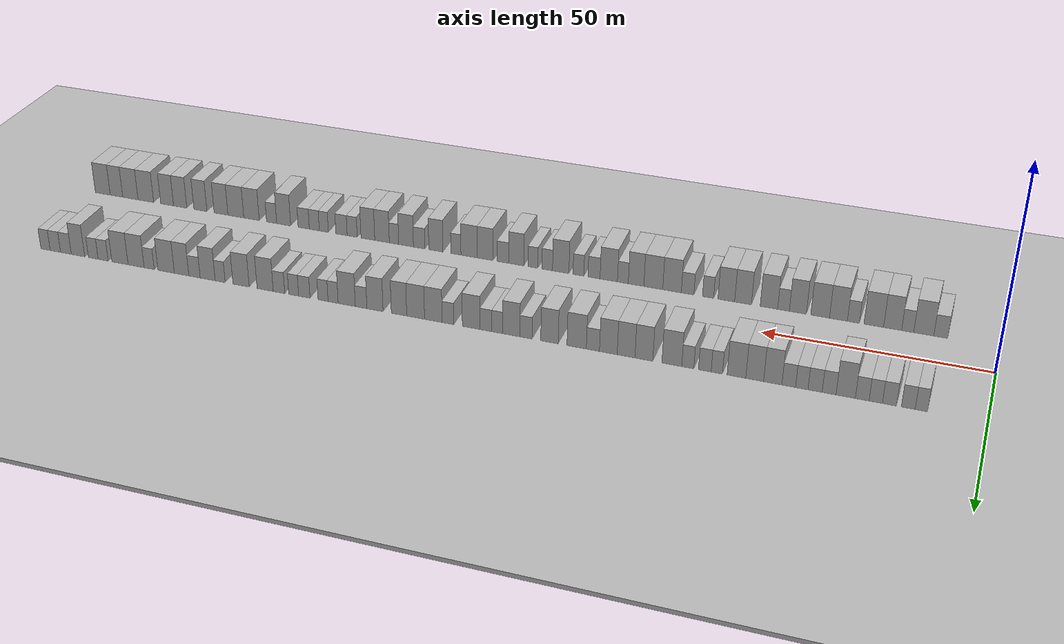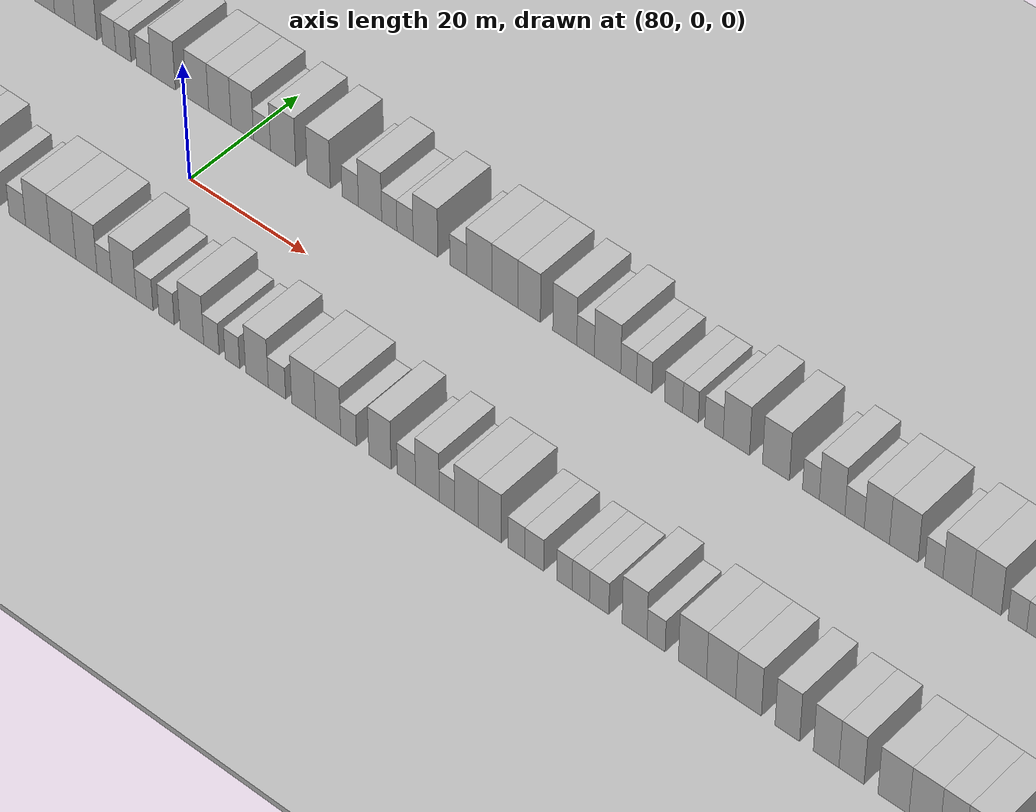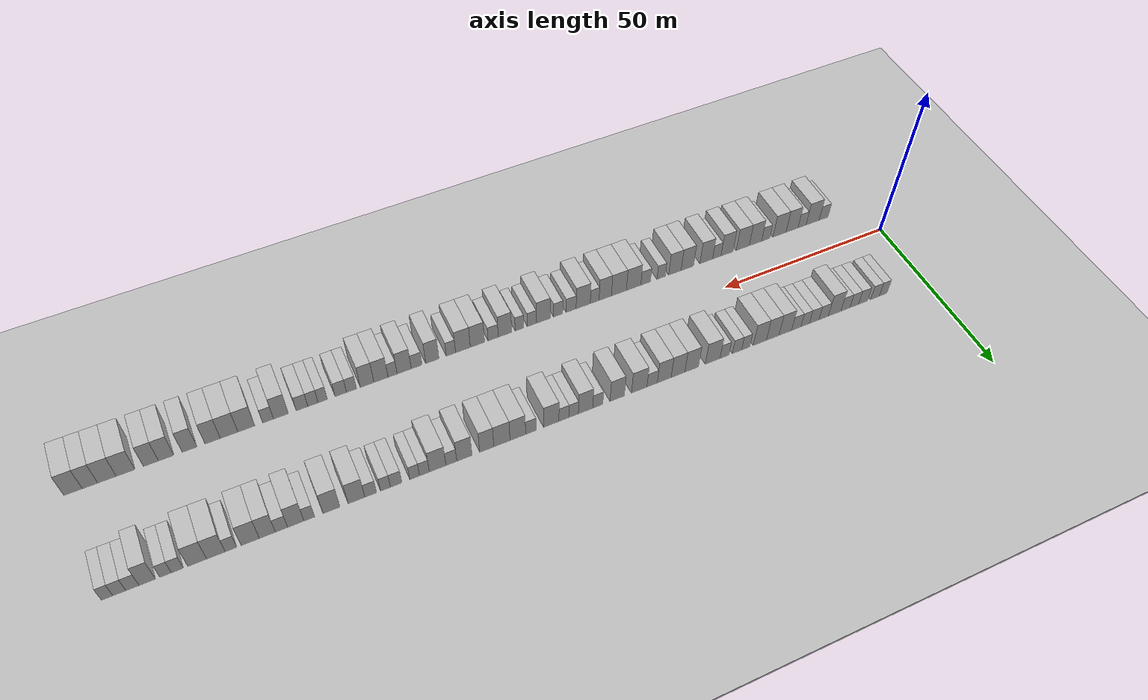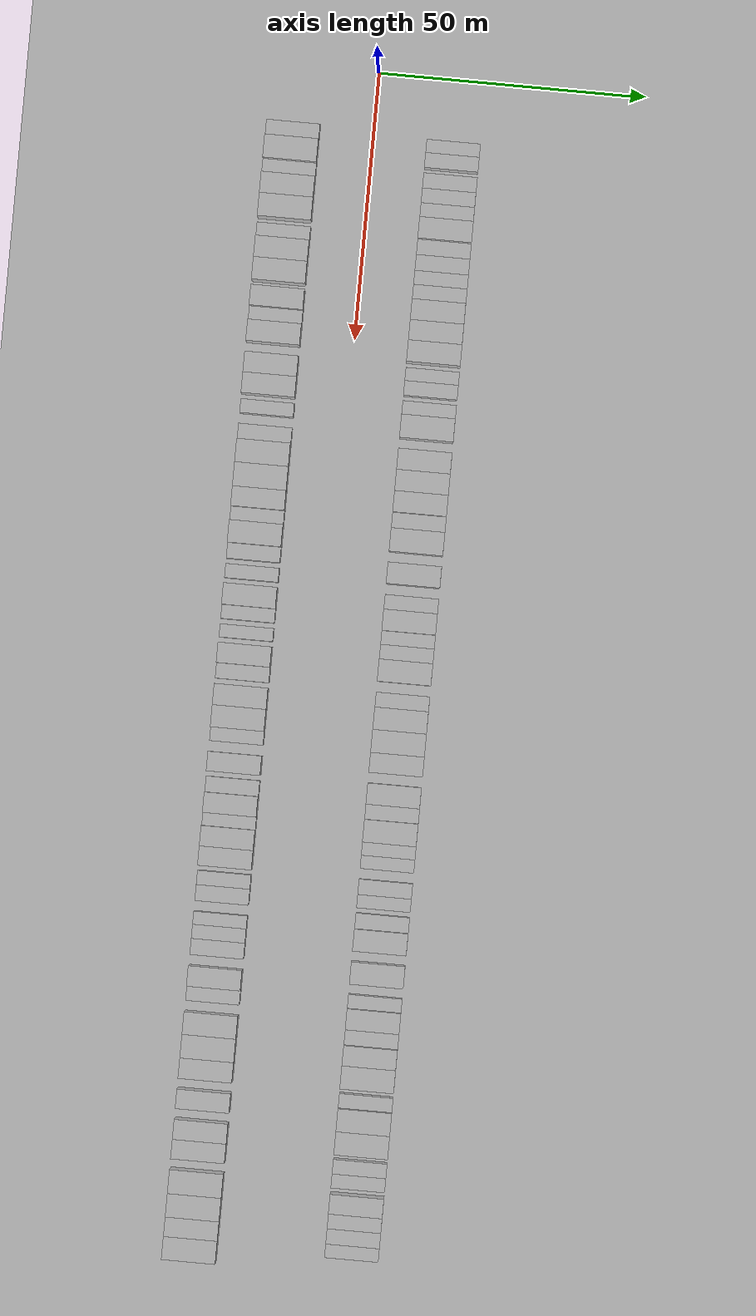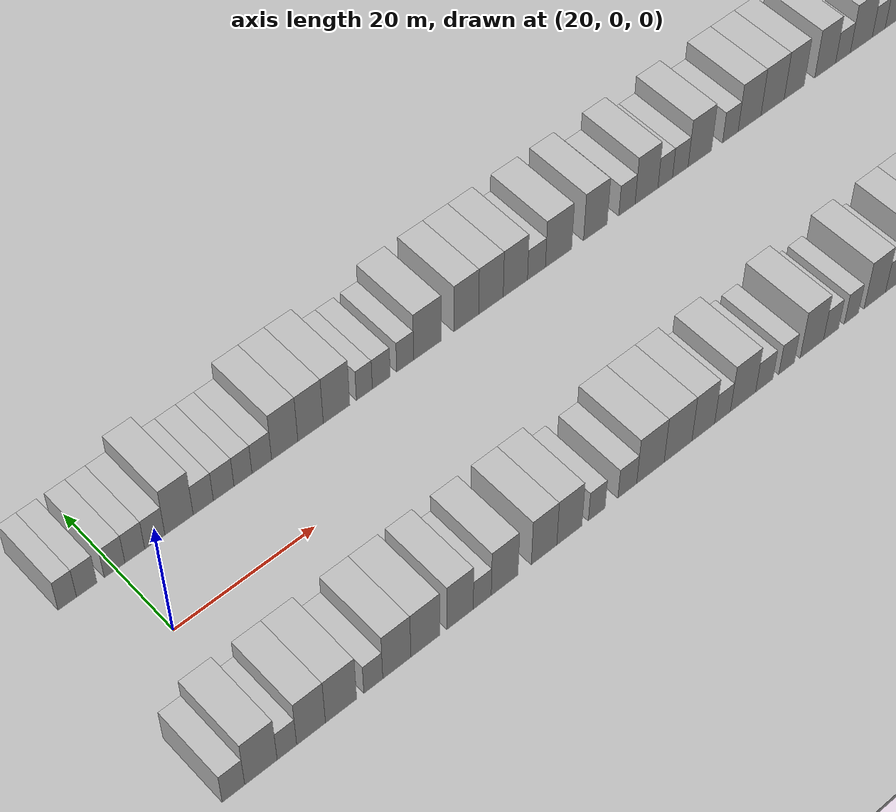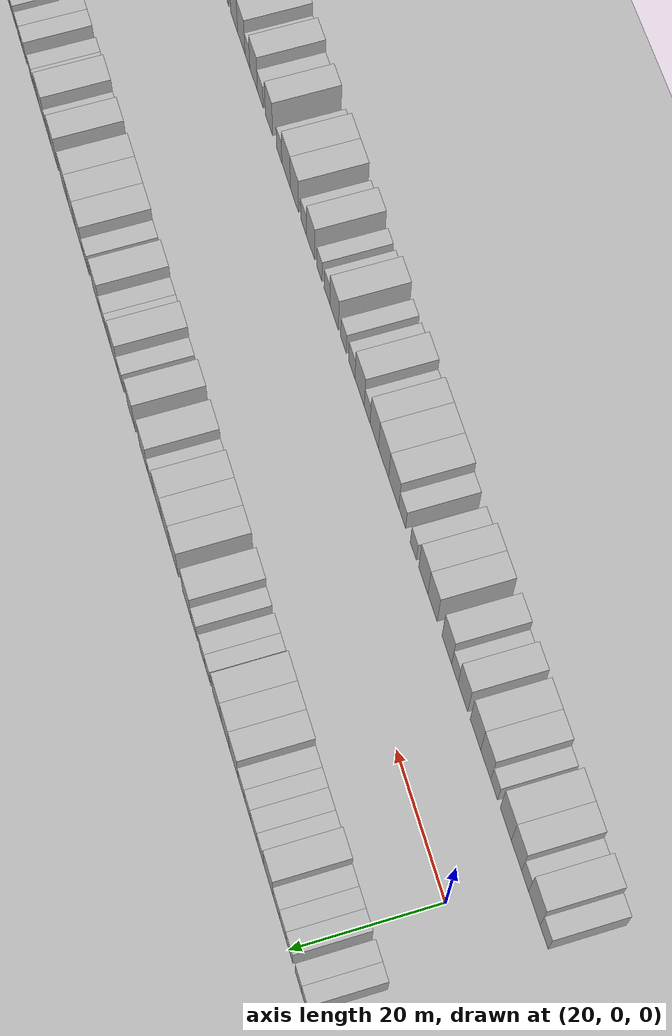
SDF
<?xml version="1.0" encoding="utf-8"?>

<sdf version="1.6">

   <world name="default">

      <gui fullscreen="0">

         <camera name="user_camera">

            <pose>-15 0 4.57585 0 0 0</pose>

            <view_controller>orbit</view_controller>

         </camera>

      </gui>

      <scene>

         <sky>

           <clouds>

             <speed>12</speed>

           </clouds>

         </sky>

         <ambient>0.4 0.4 0.4 1</ambient>

         <background>0.7 0.7 0.7 1</background>

         <shadows>1</shadows>

      </scene>

      <gravity>0 0 -9.8066</gravity>

      <magnetic_field>6e-06 2.3e-05 -4.2e-05</magnetic_field>

      <physics default="0" name="default_physics" type="ode">

         <ode>

            <solver>

               <type>quick</type>

               <iters>10</iters>

               <sor>1.0</sor>

               <use_dynamic_moi_rescaling>0</use_dynamic_moi_rescaling>

            </solver>

            <constraints>

               <cfm>0</cfm>

               <erp>0.2</erp>

               <contact_max_correcting_vel>100</contact_max_correcting_vel>

               <contact_surface_layer>0.001</contact_surface_layer>

            </constraints>

         </ode>

         <max_step_size>0.004</max_step_size>

         <real_time_factor>1</real_time_factor>

         <real_time_update_rate>250</real_time_update_rate>

      </physics>

      <light name="sun" type="directional">

         <cast_shadows>1</cast_shadows>

         <pose>0 0 10 0 0 0</pose>

         <diffuse>0.8 0.8 0.8 1</diffuse>

         <specular>0.2 0.2 0.2 1</specular>

         <attenuation>

            <range>1000</range>

            <constant>0.9</constant>

            <linear>0.01</linear>

            <quadratic>0.001</quadratic>

         </attenuation>

         <direction>-0.5 0.1 -0.9</direction>

      </light>

      <include>

         <name>ground_plane_1</name>

         <uri>model://HANNAS_ground_plane</uri>

         <pose>0 0 0  0 0 0</pose>

      </include>

      <include>

         <name>ground_plane_2</name>

         <uri>model://HANNAS_ground_plane</uri>

         <pose>100 0 0  0 0 0</pose>

      </include>

      <model name="building_1">

         <static>1</static>

         <pose frame="">13.2395 15.0000 0 0.000000 0.000000 1.570796</pose>

         <link name="link">

            <pose frame="">0 0 3.00 0 0 0</pose>

            <collision name="collision">

               <geometry>

                  <box>

                     <size>10.0000 2.4789 6.0000</size>

                  </box>

               </geometry>

               <max_contacts>10</max_contacts>

               <surface>

                  <contact>

                     <ode/>

                  </contact>

                  <bounce/>

                  <friction>

                     <torsional>

                        <ode/>

                     </torsional>

                     <ode/>

                  </friction>

               </surface>

            </collision>

            <visual name="visual">

               <cast_shadows>0</cast_shadows>

               <geometry>

                  <box>

                     <size>10.0000 2.4789 6.0000</size>

                  </box>

               </geometry>

               <material>

                  <script>

                     <uri>model://HANNAS_wall/materials/scripts</uri>

                     <uri>model://HANNAS_wall/materials/textures</uri>

                     <name>vrc/HANNAS_wall</name>

                  </script>

               </material>

            </visual>

            <self_collide>0</self_collide>

            <enable_wind>0</enable_wind>

            <kinematic>0</kinematic>

         </link>

      </model>

      <model name="building_2">

         <static>1</static>

         <pose frame="">15.8671 15.0000 0 0.000000 0.000000 1.570796</pose>

         <link name="link">

            <pose frame="">0 0 3.00 0 0 0</pose>

            <collision name="collision">

               <geometry>

                  <box>

                     <size>10.0000 2.7763 6.0000</size>

                  </box>

               </geometry>

               <max_contacts>10</max_contacts>

               <surface>

                  <contact>

                     <ode/>

                  </contact>

                  <bounce/>

                  <friction>

                     <torsional>

                        <ode/>

                     </torsional>

                     <ode/>

                  </friction>

               </surface>

            </collision>

            <visual name="visual">

               <cast_shadows>0</cast_shadows>

               <geometry>

                  <box>

                     <size>10.0000 2.7763 6.0000</size>

                  </box>

               </geometry>

               <material>

                  <script>

                     <uri>model://HANNAS_wall/materials/scripts</uri>

                     <uri>model://HANNAS_wall/materials/textures</uri>

                     <name>vrc/HANNAS_wall</name>

                  </script>

               </material>

            </visual>

            <self_collide>0</self_collide>

            <enable_wind>0</enable_wind>

            <kinematic>0</kinematic>

         </link>

      </model>

      <model name="building_3">

         <static>1</static>

         <pose frame="">19.6746 15.0000 0 0.000000 0.000000 1.570796</pose>

         <link name="link">

            <pose frame="">0 0 3.00 0 0 0</pose>

            <collision name="collision">

               <geometry>

                  <box>

                     <size>10.0000 2.8389 6.0000</size>

                  </box>

               </geometry>

               <max_contacts>10</max_contacts>

               <surface>

                  <contact>

                     <ode/>

                  </contact>

                  <bounce/>

                  <friction>

                     <torsional>

                        <ode/>

                     </torsional>

                     <ode/>

                  </friction>

               </surface>

            </collision>

            <visual name="visual">

               <cast_shadows>0</cast_shadows>

               <geometry>

                  <box>

                     <size>10.0000 2.8389 6.0000</size>

                  </box>

               </geometry>

               <material>

                  <script>

                     <uri>model://HANNAS_wall/materials/scripts</uri>

                     <uri>model://HANNAS_wall/materials/textures</uri>

                     <name>vrc/HANNAS_wall</name>

                  </script>

               </material>

            </visual>

            <self_collide>0</self_collide>

            <enable_wind>0</enable_wind>

            <kinematic>0</kinematic>

         </link>

      </model>

      <model name="building_4">

         <static>1</static>

         <pose frame="">22.4632 15.0000 0 0.000000 0.000000 1.570796</pose>

         <link name="link">

            <pose frame="">0 0 3.00 0 0 0</pose>

            <collision name="collision">

               <geometry>

                  <box>

                     <size>10.0000 2.7383 6.0000</size>

                  </box>

               </geometry>

               <max_contacts>10</max_contacts>

               <surface>

                  <contact>

                     <ode/>

                  </contact>

                  <bounce/>

                  <friction>

                     <torsional>

                        <ode/>

                     </torsional>

                     <ode/>

                  </friction>

               </surface>

            </collision>

            <visual name="visual">

               <cast_shadows>0</cast_shadows>

               <geometry>

                  <box>

                     <size>10.0000 2.7383 6.0000</size>

                  </box>

               </geometry>

               <material>

                  <script>

                     <uri>model://HANNAS_wall/materials/scripts</uri>

                     <uri>model://HANNAS_wall/materials/textures</uri>

                     <name>vrc/HANNAS_wall</name>

                  </script>

               </material>

            </visual>

            <self_collide>0</self_collide>

            <enable_wind>0</enable_wind>

            <kinematic>0</kinematic>

         </link>

      </model>

      <model name="building_5">

         <static>1</static>

         <pose frame="">25.2391 15.0000 0 0.000000 0.000000 1.570796</pose>

         <link name="link">

            <pose frame="">0 0 3.00 0 0 0</pose>

            <collision name="collision">

               <geometry>

                  <box>

                     <size>10.0000 2.8134 6.0000</size>

                  </box>

               </geometry>

               <max_contacts>10</max_contacts>

               <surface>

                  <contact>

                     <ode/>

                  </contact>

                  <bounce/>

                  <friction>

                     <torsional>

                        <ode/>

                     </torsional>

                     <ode/>

                  </friction>

               </surface>

            </collision>

            <visual name="visual">

               <cast_shadows>0</cast_shadows>

               <geometry>

                  <box>

                     <size>10.0000 2.8134 6.0000</size>

                  </box>

               </geometry>

               <material>

                  <script>

                     <uri>model://HANNAS_wall/materials/scripts</uri>

                     <uri>model://HANNAS_wall/materials/textures</uri>

                     <name>vrc/HANNAS_wall</name>

                  </script>

               </material>

            </visual>

            <self_collide>0</self_collide>

            <enable_wind>0</enable_wind>

            <kinematic>0</kinematic>

         </link>

      </model>

      <model name="building_6">

         <static>1</static>

         <pose frame="">28.6374 15.0000 0 0.000000 0.000000 1.570796</pose>

         <link name="link">

            <pose frame="">0 0 4.50 0 0 0</pose>

            <collision name="collision">

               <geometry>

                  <box>

                     <size>10.0000 3.9831 9.0000</size>

                  </box>

               </geometry>

               <max_contacts>10</max_contacts>

               <surface>

                  <contact>

                     <ode/>

                  </contact>

                  <bounce/>

                  <friction>

                     <torsional>

                        <ode/>

                     </torsional>

                     <ode/>

                  </friction>

               </surface>

            </collision>

            <visual name="visual">

               <cast_shadows>0</cast_shadows>

               <geometry>

                  <box>

                     <size>10.0000 3.9831 9.0000</size>

                  </box>

               </geometry>

               <material>

                  <script>

                     <uri>model://HANNAS_wall/materials/scripts</uri>

                     <uri>model://HANNAS_wall/materials/textures</uri>

                     <name>vrc/HANNAS_wall</name>

                  </script>

               </material>

            </visual>

            <self_collide>0</self_collide>

            <enable_wind>0</enable_wind>

            <kinematic>0</kinematic>

         </link>

      </model>

      <model name="building_7">

         <static>1</static>

         <pose frame="">32.0669 15.0000 0 0.000000 0.000000 1.570796</pose>

         <link name="link">

            <pose frame="">0 0 3.00 0 0 0</pose>

            <collision name="collision">

               <geometry>

                  <box>

                     <size>10.0000 2.8759 6.0000</size>

                  </box>

               </geometry>

               <max_contacts>10</max_contacts>

               <surface>

                  <contact>

                     <ode/>

                  </contact>

                  <bounce/>

                  <friction>

                     <torsional>

                        <ode/>

                     </torsional>

                     <ode/>

                  </friction>

               </surface>

            </collision>

            <visual name="visual">

               <cast_shadows>0</cast_shadows>

               <geometry>

                  <box>

                     <size>10.0000 2.8759 6.0000</size>

                  </box>

               </geometry>

               <material>

                  <script>

                     <uri>model://HANNAS_wall/materials/scripts</uri>

                     <uri>model://HANNAS_wall/materials/textures</uri>

                     <name>vrc/HANNAS_wall</name>

                  </script>

               </material>

            </visual>

            <self_collide>0</self_collide>

            <enable_wind>0</enable_wind>

            <kinematic>0</kinematic>

         </link>

      </model>

      <model name="building_8">

         <static>1</static>

         <pose frame="">34.9849 15.0000 0 0.000000 0.000000 1.570796</pose>

         <link name="link">

            <pose frame="">0 0 3.00 0 0 0</pose>

            <collision name="collision">

               <geometry>

                  <box>

                     <size>10.0000 2.9601 6.0000</size>

                  </box>

               </geometry>

               <max_contacts>10</max_contacts>

               <surface>

                  <contact>

                     <ode/>

                  </contact>

                  <bounce/>

                  <friction>

                     <torsional>

                        <ode/>

                     </torsional>

                     <ode/>

                  </friction>

               </surface>

            </collision>

            <visual name="visual">

               <cast_shadows>0</cast_shadows>

               <geometry>

                  <box>

                     <size>10.0000 2.9601 6.0000</size>

                  </box>

               </geometry>

               <material>

                  <script>

                     <uri>model://HANNAS_wall/materials/scripts</uri>

                     <uri>model://HANNAS_wall/materials/textures</uri>

                     <name>vrc/HANNAS_wall</name>

                  </script>

               </material>

            </visual>

            <self_collide>0</self_collide>

            <enable_wind>0</enable_wind>

            <kinematic>0</kinematic>

         </link>

      </model>

      <model name="building_9">

         <static>1</static>

         <pose frame="">37.7684 15.0000 0 0.000000 0.000000 1.570796</pose>

         <link name="link">

            <pose frame="">0 0 3.00 0 0 0</pose>

            <collision name="collision">

               <geometry>

                  <box>

                     <size>10.0000 2.6069 6.0000</size>

                  </box>

               </geometry>

               <max_contacts>10</max_contacts>

               <surface>

                  <contact>

                     <ode/>

                  </contact>

                  <bounce/>

                  <friction>

                     <torsional>

                        <ode/>

                     </torsional>

                     <ode/>

                  </friction>

               </surface>

            </collision>

            <visual name="visual">

               <cast_shadows>0</cast_shadows>

               <geometry>

                  <box>

                     <size>10.0000 2.6069 6.0000</size>

                  </box>

               </geometry>

               <material>

                  <script>

                     <uri>model://HANNAS_wall/materials/scripts</uri>

                     <uri>model://HANNAS_wall/materials/textures</uri>

                     <name>vrc/HANNAS_wall</name>

                  </script>

               </material>

            </visual>

            <self_collide>0</self_collide>

            <enable_wind>0</enable_wind>

            <kinematic>0</kinematic>

         </link>

      </model>

      <model name="building_10">

         <static>1</static>

         <pose frame="">40.5030 15.0000 0 0.000000 0.000000 1.570796</pose>

         <link name="link">

            <pose frame="">0 0 3.00 0 0 0</pose>

            <collision name="collision">

               <geometry>

                  <box>

                     <size>10.0000 2.8622 6.0000</size>

                  </box>

               </geometry>

               <max_contacts>10</max_contacts>

               <surface>

                  <contact>

                     <ode/>

                  </contact>

                  <bounce/>

                  <friction>

                     <torsional>

                        <ode/>

                     </torsional>

                     <ode/>

                  </friction>

               </surface>

            </collision>

            <visual name="visual">

               <cast_shadows>0</cast_shadows>

               <geometry>

                  <box>

                     <size>10.0000 2.8622 6.0000</size>

                  </box>

               </geometry>

               <material>

                  <script>

                     <uri>model://HANNAS_wall/materials/scripts</uri>

                     <uri>model://HANNAS_wall/materials/textures</uri>

                     <name>vrc/HANNAS_wall</name>

                  </script>

               </material>

            </visual>

            <self_collide>0</self_collide>

            <enable_wind>0</enable_wind>

            <kinematic>0</kinematic>

         </link>

      </model>

      <model name="building_11">

         <static>1</static>

         <pose frame="">43.8686 15.0000 0 0.000000 0.000000 1.570796</pose>

         <link name="link">

            <pose frame="">0 0 4.50 0 0 0</pose>

            <collision name="collision">

               <geometry>

                  <box>

                     <size>10.0000 3.8690 9.0000</size>

                  </box>

               </geometry>

               <max_contacts>10</max_contacts>

               <surface>

                  <contact>

                     <ode/>

                  </contact>

                  <bounce/>

                  <friction>

                     <torsional>

                        <ode/>

                     </torsional>

                     <ode/>

                  </friction>

               </surface>

            </collision>

            <visual name="visual">

               <cast_shadows>0</cast_shadows>

               <geometry>

                  <box>

                     <size>10.0000 3.8690 9.0000</size>

                  </box>

               </geometry>

               <material>

                  <script>

                     <uri>model://HANNAS_wall/materials/scripts</uri>

                     <uri>model://HANNAS_wall/materials/textures</uri>

                     <name>vrc/HANNAS_wall</name>

                  </script>

               </material>

            </visual>

            <self_collide>0</self_collide>

            <enable_wind>0</enable_wind>

            <kinematic>0</kinematic>

         </link>

      </model>

      <model name="building_12">

         <static>1</static>

         <pose frame="">47.6986 15.0000 0 0.000000 0.000000 1.570796</pose>

         <link name="link">

            <pose frame="">0 0 4.50 0 0 0</pose>

            <collision name="collision">

               <geometry>

                  <box>

                     <size>10.0000 3.7910 9.0000</size>

                  </box>

               </geometry>

               <max_contacts>10</max_contacts>

               <surface>

                  <contact>

                     <ode/>

                  </contact>

                  <bounce/>

                  <friction>

                     <torsional>

                        <ode/>

                     </torsional>

                     <ode/>

                  </friction>

               </surface>

            </collision>

            <visual name="visual">

               <cast_shadows>0</cast_shadows>

               <geometry>

                  <box>

                     <size>10.0000 3.7910 9.0000</size>

                  </box>

               </geometry>

               <material>

                  <script>

                     <uri>model://HANNAS_wall/materials/scripts</uri>

                     <uri>model://HANNAS_wall/materials/textures</uri>

                     <name>vrc/HANNAS_wall</name>

                  </script>

               </material>

            </visual>

            <self_collide>0</self_collide>

            <enable_wind>0</enable_wind>

            <kinematic>0</kinematic>

         </link>

      </model>

      <model name="building_13">

         <static>1</static>

         <pose frame="">51.5891 15.0000 0 0.000000 0.000000 1.570796</pose>

         <link name="link">

            <pose frame="">0 0 4.50 0 0 0</pose>

            <collision name="collision">

               <geometry>

                  <box>

                     <size>10.0000 3.9900 9.0000</size>

                  </box>

               </geometry>

               <max_contacts>10</max_contacts>

               <surface>

                  <contact>

                     <ode/>

                  </contact>

                  <bounce/>

                  <friction>

                     <torsional>

                        <ode/>

                     </torsional>

                     <ode/>

                  </friction>

               </surface>

            </collision>

            <visual name="visual">

               <cast_shadows>0</cast_shadows>

               <geometry>

                  <box>

                     <size>10.0000 3.9900 9.0000</size>

                  </box>

               </geometry>

               <material>

                  <script>

                     <uri>model://HANNAS_wall/materials/scripts</uri>

                     <uri>model://HANNAS_wall/materials/textures</uri>

                     <name>vrc/HANNAS_wall</name>

                  </script>

               </material>

            </visual>

            <self_collide>0</self_collide>

            <enable_wind>0</enable_wind>

            <kinematic>0</kinematic>

         </link>

      </model>

      <model name="building_14">

         <static>1</static>

         <pose frame="">55.8028 15.0000 0 0.000000 0.000000 1.570796</pose>

         <link name="link">

            <pose frame="">0 0 3.00 0 0 0</pose>

            <collision name="collision">

               <geometry>

                  <box>

                     <size>10.0000 2.4374 6.0000</size>

                  </box>

               </geometry>

               <max_contacts>10</max_contacts>

               <surface>

                  <contact>

                     <ode/>

                  </contact>

                  <bounce/>

                  <friction>

                     <torsional>

                        <ode/>

                     </torsional>

                     <ode/>

                  </friction>

               </surface>

            </collision>

            <visual name="visual">

               <cast_shadows>0</cast_shadows>

               <geometry>

                  <box>

                     <size>10.0000 2.4374 6.0000</size>

                  </box>

               </geometry>

               <material>

                  <script>

                     <uri>model://HANNAS_wall/materials/scripts</uri>

                     <uri>model://HANNAS_wall/materials/textures</uri>

                     <name>vrc/HANNAS_wall</name>

                  </script>

               </material>

            </visual>

            <self_collide>0</self_collide>

            <enable_wind>0</enable_wind>

            <kinematic>0</kinematic>

         </link>

      </model>

      <model name="building_15">

         <static>1</static>

         <pose frame="">58.3949 15.0000 0 0.000000 0.000000 1.570796</pose>

         <link name="link">

            <pose frame="">0 0 3.00 0 0 0</pose>

            <collision name="collision">

               <geometry>

                  <box>

                     <size>10.0000 2.7468 6.0000</size>

                  </box>

               </geometry>

               <max_contacts>10</max_contacts>

               <surface>

                  <contact>

                     <ode/>

                  </contact>

                  <bounce/>

                  <friction>

                     <torsional>

                        <ode/>

                     </torsional>

                     <ode/>

                  </friction>

               </surface>

            </collision>

            <visual name="visual">

               <cast_shadows>0</cast_shadows>

               <geometry>

                  <box>

                     <size>10.0000 2.7468 6.0000</size>

                  </box>

               </geometry>

               <material>

                  <script>

                     <uri>model://HANNAS_wall/materials/scripts</uri>

                     <uri>model://HANNAS_wall/materials/textures</uri>

                     <name>vrc/HANNAS_wall</name>

                  </script>

               </material>

            </visual>

            <self_collide>0</self_collide>

            <enable_wind>0</enable_wind>

            <kinematic>0</kinematic>

         </link>

      </model>

      <model name="building_16">

         <static>1</static>

         <pose frame="">62.0917 15.0000 0 0.000000 0.000000 1.570796</pose>

         <link name="link">

            <pose frame="">0 0 3.00 0 0 0</pose>

            <collision name="collision">

               <geometry>

                  <box>

                     <size>10.0000 2.6467 6.0000</size>

                  </box>

               </geometry>

               <max_contacts>10</max_contacts>

               <surface>

                  <contact>

                     <ode/>

                  </contact>

                  <bounce/>

                  <friction>

                     <torsional>

                        <ode/>

                     </torsional>

                     <ode/>

                  </friction>

               </surface>

            </collision>

            <visual name="visual">

               <cast_shadows>0</cast_shadows>

               <geometry>

                  <box>

                     <size>10.0000 2.6467 6.0000</size>

                  </box>

               </geometry>

               <material>

                  <script>

                     <uri>model://HANNAS_wall/materials/scripts</uri>

                     <uri>model://HANNAS_wall/materials/textures</uri>

                     <name>vrc/HANNAS_wall</name>

                  </script>

               </material>

            </visual>

            <self_collide>0</self_collide>

            <enable_wind>0</enable_wind>

            <kinematic>0</kinematic>

         </link>

      </model>

      <model name="building_17">

         <static>1</static>

         <pose frame="">65.5790 15.0000 0 0.000000 0.000000 1.570796</pose>

         <link name="link">

            <pose frame="">0 0 4.50 0 0 0</pose>

            <collision name="collision">

               <geometry>

                  <box>

                     <size>10.0000 4.3279 9.0000</size>

                  </box>

               </geometry>

               <max_contacts>10</max_contacts>

               <surface>

                  <contact>

                     <ode/>

                  </contact>

                  <bounce/>

                  <friction>

                     <torsional>

                        <ode/>

                     </torsional>

                     <ode/>

                  </friction>

               </surface>

            </collision>

            <visual name="visual">

               <cast_shadows>0</cast_shadows>

               <geometry>

                  <box>

                     <size>10.0000 4.3279 9.0000</size>

                  </box>

               </geometry>

               <material>

                  <script>

                     <uri>model://HANNAS_wall/materials/scripts</uri>

                     <uri>model://HANNAS_wall/materials/textures</uri>

                     <name>vrc/HANNAS_wall</name>

                  </script>

               </material>

            </visual>

            <self_collide>0</self_collide>

            <enable_wind>0</enable_wind>

            <kinematic>0</kinematic>

         </link>

      </model>

      <model name="building_18">

         <static>1</static>

         <pose frame="">71.7157 15.0000 0 0.000000 0.000000 1.570796</pose>

         <link name="link">

            <pose frame="">0 0 4.50 0 0 0</pose>

            <collision name="collision">

               <geometry>

                  <box>

                     <size>10.0000 3.9455 9.0000</size>

                  </box>

               </geometry>

               <max_contacts>10</max_contacts>

               <surface>

                  <contact>

                     <ode/>

                  </contact>

                  <bounce/>

                  <friction>

                     <torsional>

                        <ode/>

                     </torsional>

                     <ode/>

                  </friction>

               </surface>

            </collision>

            <visual name="visual">

               <cast_shadows>0</cast_shadows>

               <geometry>

                  <box>

                     <size>10.0000 3.9455 9.0000</size>

                  </box>

               </geometry>

               <material>

                  <script>

                     <uri>model://HANNAS_wall/materials/scripts</uri>

                     <uri>model://HANNAS_wall/materials/textures</uri>

                     <name>vrc/HANNAS_wall</name>

                  </script>

               </material>

            </visual>

            <self_collide>0</self_collide>

            <enable_wind>0</enable_wind>

            <kinematic>0</kinematic>

         </link>

      </model>

      <model name="building_19">

         <static>1</static>

         <pose frame="">75.6649 15.0000 0 0.000000 0.000000 1.570796</pose>

         <link name="link">

            <pose frame="">0 0 4.50 0 0 0</pose>

            <collision name="collision">

               <geometry>

                  <box>

                     <size>10.0000 3.9529 9.0000</size>

                  </box>

               </geometry>

               <max_contacts>10</max_contacts>

               <surface>

                  <contact>

                     <ode/>

                  </contact>

                  <bounce/>

                  <friction>

                     <torsional>

                        <ode/>

                     </torsional>

                     <ode/>

                  </friction>

               </surface>

            </collision>

            <visual name="visual">

               <cast_shadows>0</cast_shadows>

               <geometry>

                  <box>

                     <size>10.0000 3.9529 9.0000</size>

                  </box>

               </geometry>

               <material>

                  <script>

                     <uri>model://HANNAS_wall/materials/scripts</uri>

                     <uri>model://HANNAS_wall/materials/textures</uri>

                     <name>vrc/HANNAS_wall</name>

                  </script>

               </material>

            </visual>

            <self_collide>0</self_collide>

            <enable_wind>0</enable_wind>

            <kinematic>0</kinematic>

         </link>

      </model>

      <model name="building_20">

         <static>1</static>

         <pose frame="">79.6231 15.0000 0 0.000000 0.000000 1.570796</pose>

         <link name="link">

            <pose frame="">0 0 4.50 0 0 0</pose>

            <collision name="collision">

               <geometry>

                  <box>

                     <size>10.0000 3.9635 9.0000</size>

                  </box>

               </geometry>

               <max_contacts>10</max_contacts>

               <surface>

                  <contact>

                     <ode/>

                  </contact>

                  <bounce/>

                  <friction>

                     <torsional>

                        <ode/>

                     </torsional>

                     <ode/>

                  </friction>

               </surface>

            </collision>

            <visual name="visual">

               <cast_shadows>0</cast_shadows>

               <geometry>

                  <box>

                     <size>10.0000 3.9635 9.0000</size>

                  </box>

               </geometry>

               <material>

                  <script>

                     <uri>model://HANNAS_wall/materials/scripts</uri>

                     <uri>model://HANNAS_wall/materials/textures</uri>

                     <name>vrc/HANNAS_wall</name>

                  </script>

               </material>

            </visual>

            <self_collide>0</self_collide>

            <enable_wind>0</enable_wind>

            <kinematic>0</kinematic>

         </link>

      </model>

      <model name="building_21">

         <static>1</static>

         <pose frame="">83.0800 15.0000 0 0.000000 0.000000 1.570796</pose>

         <link name="link">

            <pose frame="">0 0 3.00 0 0 0</pose>

            <collision name="collision">

               <geometry>

                  <box>

                     <size>10.0000 2.9503 6.0000</size>

                  </box>

               </geometry>

               <max_contacts>10</max_contacts>

               <surface>

                  <contact>

                     <ode/>

                  </contact>

                  <bounce/>

                  <friction>

                     <torsional>

                        <ode/>

                     </torsional>

                     <ode/>

                  </friction>

               </surface>

            </collision>

            <visual name="visual">

               <cast_shadows>0</cast_shadows>

               <geometry>

                  <box>

                     <size>10.0000 2.9503 6.0000</size>

                  </box>

               </geometry>

               <material>

                  <script>

                     <uri>model://HANNAS_wall/materials/scripts</uri>

                     <uri>model://HANNAS_wall/materials/textures</uri>

                     <name>vrc/HANNAS_wall</name>

                  </script>

               </material>

            </visual>

            <self_collide>0</self_collide>

            <enable_wind>0</enable_wind>

            <kinematic>0</kinematic>

         </link>

      </model>

      <model name="building_22">

         <static>1</static>

         <pose frame="">86.7415 15.0000 0 0.000000 0.000000 1.570796</pose>

         <link name="link">

            <pose frame="">0 0 4.50 0 0 0</pose>

            <collision name="collision">

               <geometry>

                  <box>

                     <size>10.0000 4.3728 9.0000</size>

                  </box>

               </geometry>

               <max_contacts>10</max_contacts>

               <surface>

                  <contact>

                     <ode/>

                  </contact>

                  <bounce/>

                  <friction>

                     <torsional>

                        <ode/>

                     </torsional>

                     <ode/>

                  </friction>

               </surface>

            </collision>

            <visual name="visual">

               <cast_shadows>0</cast_shadows>

               <geometry>

                  <box>

                     <size>10.0000 4.3728 9.0000</size>

                  </box>

               </geometry>

               <material>

                  <script>

                     <uri>model://HANNAS_wall/materials/scripts</uri>

                     <uri>model://HANNAS_wall/materials/textures</uri>

                     <name>vrc/HANNAS_wall</name>

                  </script>

               </material>

            </visual>

            <self_collide>0</self_collide>

            <enable_wind>0</enable_wind>

            <kinematic>0</kinematic>

         </link>

      </model>

      <model name="building_23">

         <static>1</static>

         <pose frame="">92.9218 15.0000 0 0.000000 0.000000 1.570796</pose>

         <link name="link">

            <pose frame="">0 0 4.50 0 0 0</pose>

            <collision name="collision">

               <geometry>

                  <box>

                     <size>10.0000 3.9877 9.0000</size>

                  </box>

               </geometry>

               <max_contacts>10</max_contacts>

               <surface>

                  <contact>

                     <ode/>

                  </contact>

                  <bounce/>

                  <friction>

                     <torsional>

                        <ode/>

                     </torsional>

                     <ode/>

                  </friction>

               </surface>

            </collision>

            <visual name="visual">

               <cast_shadows>0</cast_shadows>

               <geometry>

                  <box>

                     <size>10.0000 3.9877 9.0000</size>

                  </box>

               </geometry>

               <material>

                  <script>

                     <uri>model://HANNAS_wall/materials/scripts</uri>

                     <uri>model://HANNAS_wall/materials/textures</uri>

                     <name>vrc/HANNAS_wall</name>

                  </script>

               </material>

            </visual>

            <self_collide>0</self_collide>

            <enable_wind>0</enable_wind>

            <kinematic>0</kinematic>

         </link>

      </model>

      <model name="building_24">

         <static>1</static>

         <pose frame="">98.3099 15.0000 0 0.000000 0.000000 1.570796</pose>

         <link name="link">

            <pose frame="">0 0 3.00 0 0 0</pose>

            <collision name="collision">

               <geometry>

                  <box>

                     <size>10.0000 2.7886 6.0000</size>

                  </box>

               </geometry>

               <max_contacts>10</max_contacts>

               <surface>

                  <contact>

                     <ode/>

                  </contact>

                  <bounce/>

                  <friction>

                     <torsional>

                        <ode/>

                     </torsional>

                     <ode/>

                  </friction>

               </surface>

            </collision>

            <visual name="visual">

               <cast_shadows>0</cast_shadows>

               <geometry>

                  <box>

                     <size>10.0000 2.7886 6.0000</size>

                  </box>

               </geometry>

               <material>

                  <script>

                     <uri>model://HANNAS_wall/materials/scripts</uri>

                     <uri>model://HANNAS_wall/materials/textures</uri>

                     <name>vrc/HANNAS_wall</name>

                  </script>

               </material>

            </visual>

            <self_collide>0</self_collide>

            <enable_wind>0</enable_wind>

            <kinematic>0</kinematic>

         </link>

      </model>

      <model name="building_25">

         <static>1</static>

         <pose frame="">101.6872 15.0000 0 0.000000 0.000000 1.570796</pose>

         <link name="link">

            <pose frame="">0 0 4.50 0 0 0</pose>

            <collision name="collision">

               <geometry>

                  <box>

                     <size>10.0000 3.9659 9.0000</size>

                  </box>

               </geometry>

               <max_contacts>10</max_contacts>

               <surface>

                  <contact>

                     <ode/>

                  </contact>

                  <bounce/>

                  <friction>

                     <torsional>

                        <ode/>

                     </torsional>

                     <ode/>

                  </friction>

               </surface>

            </collision>

            <visual name="visual">

               <cast_shadows>0</cast_shadows>

               <geometry>

                  <box>

                     <size>10.0000 3.9659 9.0000</size>

                  </box>

               </geometry>

               <material>

                  <script>

                     <uri>model://HANNAS_wall/materials/scripts</uri>

                     <uri>model://HANNAS_wall/materials/textures</uri>

                     <name>vrc/HANNAS_wall</name>

                  </script>

               </material>

            </visual>

            <self_collide>0</self_collide>

            <enable_wind>0</enable_wind>

            <kinematic>0</kinematic>

         </link>

      </model>

      <model name="building_26">

         <static>1</static>

         <pose frame="">104.9479 15.0000 0 0.000000 0.000000 1.570796</pose>

         <link name="link">

            <pose frame="">0 0 3.00 0 0 0</pose>

            <collision name="collision">

               <geometry>

                  <box>

                     <size>10.0000 2.5557 6.0000</size>

                  </box>

               </geometry>

               <max_contacts>10</max_contacts>

               <surface>

                  <contact>

                     <ode/>

                  </contact>

                  <bounce/>

                  <friction>

                     <torsional>

                        <ode/>

                     </torsional>

                     <ode/>

                  </friction>

               </surface>

            </collision>

            <visual name="visual">

               <cast_shadows>0</cast_shadows>

               <geometry>

                  <box>

                     <size>10.0000 2.5557 6.0000</size>

                  </box>

               </geometry>

               <material>

                  <script>

                     <uri>model://HANNAS_wall/materials/scripts</uri>

                     <uri>model://HANNAS_wall/materials/textures</uri>

                     <name>vrc/HANNAS_wall</name>

                  </script>

               </material>

            </visual>

            <self_collide>0</self_collide>

            <enable_wind>0</enable_wind>

            <kinematic>0</kinematic>

         </link>

      </model>

      <model name="building_27">

         <static>1</static>

         <pose frame="">107.5997 15.0000 0 0.000000 0.000000 1.570796</pose>

         <link name="link">

            <pose frame="">0 0 3.00 0 0 0</pose>

            <collision name="collision">

               <geometry>

                  <box>

                     <size>10.0000 2.7478 6.0000</size>

                  </box>

               </geometry>

               <max_contacts>10</max_contacts>

               <surface>

                  <contact>

                     <ode/>

                  </contact>

                  <bounce/>

                  <friction>

                     <torsional>

                        <ode/>

                     </torsional>

                     <ode/>

                  </friction>

               </surface>

            </collision>

            <visual name="visual">

               <cast_shadows>0</cast_shadows>

               <geometry>

                  <box>

                     <size>10.0000 2.7478 6.0000</size>

                  </box>

               </geometry>

               <material>

                  <script>

                     <uri>model://HANNAS_wall/materials/scripts</uri>

                     <uri>model://HANNAS_wall/materials/textures</uri>

                     <name>vrc/HANNAS_wall</name>

                  </script>

               </material>

            </visual>

            <self_collide>0</self_collide>

            <enable_wind>0</enable_wind>

            <kinematic>0</kinematic>

         </link>

      </model>

      <model name="building_28">

         <static>1</static>

         <pose frame="">111.0488 15.0000 0 0.000000 0.000000 1.570796</pose>

         <link name="link">

            <pose frame="">0 0 4.50 0 0 0</pose>

            <collision name="collision">

               <geometry>

                  <box>

                     <size>10.0000 4.1505 9.0000</size>

                  </box>

               </geometry>

               <max_contacts>10</max_contacts>

               <surface>

                  <contact>

                     <ode/>

                  </contact>

                  <bounce/>

                  <friction>

                     <torsional>

                        <ode/>

                     </torsional>

                     <ode/>

                  </friction>

               </surface>

            </collision>

            <visual name="visual">

               <cast_shadows>0</cast_shadows>

               <geometry>

                  <box>

                     <size>10.0000 4.1505 9.0000</size>

                  </box>

               </geometry>

               <material>

                  <script>

                     <uri>model://HANNAS_wall/materials/scripts</uri>

                     <uri>model://HANNAS_wall/materials/textures</uri>

                     <name>vrc/HANNAS_wall</name>

                  </script>

               </material>

            </visual>

            <self_collide>0</self_collide>

            <enable_wind>0</enable_wind>

            <kinematic>0</kinematic>

         </link>

      </model>

      <model name="building_29">

         <static>1</static>

         <pose frame="">116.5231 15.0000 0 0.000000 0.000000 1.570796</pose>

         <link name="link">

            <pose frame="">0 0 3.00 0 0 0</pose>

            <collision name="collision">

               <geometry>

                  <box>

                     <size>10.0000 2.7981 6.0000</size>

                  </box>

               </geometry>

               <max_contacts>10</max_contacts>

               <surface>

                  <contact>

                     <ode/>

                  </contact>

                  <bounce/>

                  <friction>

                     <torsional>

                        <ode/>

                     </torsional>

                     <ode/>

                  </friction>

               </surface>

            </collision>

            <visual name="visual">

               <cast_shadows>0</cast_shadows>

               <geometry>

                  <box>

                     <size>10.0000 2.7981 6.0000</size>

                  </box>

               </geometry>

               <material>

                  <script>

                     <uri>model://HANNAS_wall/materials/scripts</uri>

                     <uri>model://HANNAS_wall/materials/textures</uri>

                     <name>vrc/HANNAS_wall</name>

                  </script>

               </material>

            </visual>

            <self_collide>0</self_collide>

            <enable_wind>0</enable_wind>

            <kinematic>0</kinematic>

         </link>

      </model>

      <model name="building_30">

         <static>1</static>

         <pose frame="">120.0027 15.0000 0 0.000000 0.000000 1.570796</pose>

         <link name="link">

            <pose frame="">0 0 4.50 0 0 0</pose>

            <collision name="collision">

               <geometry>

                  <box>

                     <size>10.0000 4.1611 9.0000</size>

                  </box>

               </geometry>

               <max_contacts>10</max_contacts>

               <surface>

                  <contact>

                     <ode/>

                  </contact>

                  <bounce/>

                  <friction>

                     <torsional>

                        <ode/>

                     </torsional>

                     <ode/>

                  </friction>

               </surface>

            </collision>

            <visual name="visual">

               <cast_shadows>0</cast_shadows>

               <geometry>

                  <box>

                     <size>10.0000 4.1611 9.0000</size>

                  </box>

               </geometry>

               <material>

                  <script>

                     <uri>model://HANNAS_wall/materials/scripts</uri>

                     <uri>model://HANNAS_wall/materials/textures</uri>

                     <name>vrc/HANNAS_wall</name>

                  </script>

               </material>

            </visual>

            <self_collide>0</self_collide>

            <enable_wind>0</enable_wind>

            <kinematic>0</kinematic>

         </link>

      </model>

      <model name="building_31">

         <static>1</static>

         <pose frame="">124.2219 15.0000 0 0.000000 0.000000 1.570796</pose>

         <link name="link">

            <pose frame="">0 0 4.50 0 0 0</pose>

            <collision name="collision">

               <geometry>

                  <box>

                     <size>10.0000 4.2773 9.0000</size>

                  </box>

               </geometry>

               <max_contacts>10</max_contacts>

               <surface>

                  <contact>

                     <ode/>

                  </contact>

                  <bounce/>

                  <friction>

                     <torsional>

                        <ode/>

                     </torsional>

                     <ode/>

                  </friction>

               </surface>

            </collision>

            <visual name="visual">

               <cast_shadows>0</cast_shadows>

               <geometry>

                  <box>

                     <size>10.0000 4.2773 9.0000</size>

                  </box>

               </geometry>

               <material>

                  <script>

                     <uri>model://HANNAS_wall/materials/scripts</uri>

                     <uri>model://HANNAS_wall/materials/textures</uri>

                     <name>vrc/HANNAS_wall</name>

                  </script>

               </material>

            </visual>

            <self_collide>0</self_collide>

            <enable_wind>0</enable_wind>

            <kinematic>0</kinematic>

         </link>

      </model>

      <model name="building_32">

         <static>1</static>

         <pose frame="">128.2122 15.0000 0 0.000000 0.000000 1.570796</pose>

         <link name="link">

            <pose frame="">0 0 4.50 0 0 0</pose>

            <collision name="collision">

               <geometry>

                  <box>

                     <size>10.0000 3.7033 9.0000</size>

                  </box>

               </geometry>

               <max_contacts>10</max_contacts>

               <surface>

                  <contact>

                     <ode/>

                  </contact>

                  <bounce/>

                  <friction>

                     <torsional>

                        <ode/>

                     </torsional>

                     <ode/>

                  </friction>

               </surface>

            </collision>

            <visual name="visual">

               <cast_shadows>0</cast_shadows>

               <geometry>

                  <box>

                     <size>10.0000 3.7033 9.0000</size>

                  </box>

               </geometry>

               <material>

                  <script>

                     <uri>model://HANNAS_wall/materials/scripts</uri>

                     <uri>model://HANNAS_wall/materials/textures</uri>

                     <name>vrc/HANNAS_wall</name>

                  </script>

               </material>

            </visual>

            <self_collide>0</self_collide>

            <enable_wind>0</enable_wind>

            <kinematic>0</kinematic>

         </link>

      </model>

      <model name="building_33">

         <static>1</static>

         <pose frame="">134.0281 15.0000 0 0.000000 0.000000 1.570796</pose>

         <link name="link">

            <pose frame="">0 0 4.50 0 0 0</pose>

            <collision name="collision">

               <geometry>

                  <box>

                     <size>10.0000 3.9285 9.0000</size>

                  </box>

               </geometry>

               <max_contacts>10</max_contacts>

               <surface>

                  <contact>

                     <ode/>

                  </contact>

                  <bounce/>

                  <friction>

                     <torsional>

                        <ode/>

                     </torsional>

                     <ode/>

                  </friction>

               </surface>

            </collision>

            <visual name="visual">

               <cast_shadows>0</cast_shadows>

               <geometry>

                  <box>

                     <size>10.0000 3.9285 9.0000</size>

                  </box>

               </geometry>

               <material>

                  <script>

                     <uri>model://HANNAS_wall/materials/scripts</uri>

                     <uri>model://HANNAS_wall/materials/textures</uri>

                     <name>vrc/HANNAS_wall</name>

                  </script>

               </material>

            </visual>

            <self_collide>0</self_collide>

            <enable_wind>0</enable_wind>

            <kinematic>0</kinematic>

         </link>

      </model>

      <model name="building_34">

         <static>1</static>

         <pose frame="">137.4024 15.0000 0 0.000000 0.000000 1.570796</pose>

         <link name="link">

            <pose frame="">0 0 3.00 0 0 0</pose>

            <collision name="collision">

               <geometry>

                  <box>

                     <size>10.0000 2.8201 6.0000</size>

                  </box>

               </geometry>

               <max_contacts>10</max_contacts>

               <surface>

                  <contact>

                     <ode/>

                  </contact>

                  <bounce/>

                  <friction>

                     <torsional>

                        <ode/>

                     </torsional>

                     <ode/>

                  </friction>

               </surface>

            </collision>

            <visual name="visual">

               <cast_shadows>0</cast_shadows>

               <geometry>

                  <box>

                     <size>10.0000 2.8201 6.0000</size>

                  </box>

               </geometry>

               <material>

                  <script>

                     <uri>model://HANNAS_wall/materials/scripts</uri>

                     <uri>model://HANNAS_wall/materials/textures</uri>

                     <name>vrc/HANNAS_wall</name>

                  </script>

               </material>

            </visual>

            <self_collide>0</self_collide>

            <enable_wind>0</enable_wind>

            <kinematic>0</kinematic>

         </link>

      </model>

      <model name="building_35">

         <static>1</static>

         <pose frame="">140.9218 15.0000 0 0.000000 0.000000 1.570796</pose>

         <link name="link">

            <pose frame="">0 0 4.50 0 0 0</pose>

            <collision name="collision">

               <geometry>

                  <box>

                     <size>10.0000 4.2188 9.0000</size>

                  </box>

               </geometry>

               <max_contacts>10</max_contacts>

               <surface>

                  <contact>

                     <ode/>

                  </contact>

                  <bounce/>

                  <friction>

                     <torsional>

                        <ode/>

                     </torsional>

                     <ode/>

                  </friction>

               </surface>

            </collision>

            <visual name="visual">

               <cast_shadows>0</cast_shadows>

               <geometry>

                  <box>

                     <size>10.0000 4.2188 9.0000</size>

                  </box>

               </geometry>

               <material>

                  <script>

                     <uri>model://HANNAS_wall/materials/scripts</uri>

                     <uri>model://HANNAS_wall/materials/textures</uri>

                     <name>vrc/HANNAS_wall</name>

                  </script>

               </material>

            </visual>

            <self_collide>0</self_collide>

            <enable_wind>0</enable_wind>

            <kinematic>0</kinematic>

         </link>

      </model>

      <model name="building_36">

         <static>1</static>

         <pose frame="">144.2823 15.0000 0 0.000000 0.000000 1.570796</pose>

         <link name="link">

            <pose frame="">0 0 3.00 0 0 0</pose>

            <collision name="collision">

               <geometry>

                  <box>

                     <size>10.0000 2.5022 6.0000</size>

                  </box>

               </geometry>

               <max_contacts>10</max_contacts>

               <surface>

                  <contact>

                     <ode/>

                  </contact>

                  <bounce/>

                  <friction>

                     <torsional>

                        <ode/>

                     </torsional>

                     <ode/>

                  </friction>

               </surface>

            </collision>

            <visual name="visual">

               <cast_shadows>0</cast_shadows>

               <geometry>

                  <box>

                     <size>10.0000 2.5022 6.0000</size>

                  </box>

               </geometry>

               <material>

                  <script>

                     <uri>model://HANNAS_wall/materials/scripts</uri>

                     <uri>model://HANNAS_wall/materials/textures</uri>

                     <name>vrc/HANNAS_wall</name>

                  </script>

               </material>

            </visual>

            <self_collide>0</self_collide>

            <enable_wind>0</enable_wind>

            <kinematic>0</kinematic>

         </link>

      </model>

      <model name="building_37">

         <static>1</static>

         <pose frame="">146.7636 15.0000 0 0.000000 0.000000 1.570796</pose>

         <link name="link">

            <pose frame="">0 0 3.00 0 0 0</pose>

            <collision name="collision">

               <geometry>

                  <box>

                     <size>10.0000 2.4604 6.0000</size>

                  </box>

               </geometry>

               <max_contacts>10</max_contacts>

               <surface>

                  <contact>

                     <ode/>

                  </contact>

                  <bounce/>

                  <friction>

                     <torsional>

                        <ode/>

                     </torsional>

                     <ode/>

                  </friction>

               </surface>

            </collision>

            <visual name="visual">

               <cast_shadows>0</cast_shadows>

               <geometry>

                  <box>

                     <size>10.0000 2.4604 6.0000</size>

                  </box>

               </geometry>

               <material>

                  <script>

                     <uri>model://HANNAS_wall/materials/scripts</uri>

                     <uri>model://HANNAS_wall/materials/textures</uri>

                     <name>vrc/HANNAS_wall</name>

                  </script>

               </material>

            </visual>

            <self_collide>0</self_collide>

            <enable_wind>0</enable_wind>

            <kinematic>0</kinematic>

         </link>

      </model>

      <model name="building_38">

         <static>1</static>

         <pose frame="">151.4189 15.0000 0 0.000000 0.000000 1.570796</pose>

         <link name="link">

            <pose frame="">0 0 3.00 0 0 0</pose>

            <collision name="collision">

               <geometry>

                  <box>

                     <size>10.0000 2.8504 6.0000</size>

                  </box>

               </geometry>

               <max_contacts>10</max_contacts>

               <surface>

                  <contact>

                     <ode/>

                  </contact>

                  <bounce/>

                  <friction>

                     <torsional>

                        <ode/>

                     </torsional>

                     <ode/>

                  </friction>

               </surface>

            </collision>

            <visual name="visual">

               <cast_shadows>0</cast_shadows>

               <geometry>

                  <box>

                     <size>10.0000 2.8504 6.0000</size>

                  </box>

               </geometry>

               <material>

                  <script>

                     <uri>model://HANNAS_wall/materials/scripts</uri>

                     <uri>model://HANNAS_wall/materials/textures</uri>

                     <name>vrc/HANNAS_wall</name>

                  </script>

               </material>

            </visual>

            <self_collide>0</self_collide>

            <enable_wind>0</enable_wind>

            <kinematic>0</kinematic>

         </link>

      </model>

      <model name="building_39">

         <static>1</static>

         <pose frame="">154.0806 15.0000 0 0.000000 0.000000 1.570796</pose>

         <link name="link">

            <pose frame="">0 0 3.00 0 0 0</pose>

            <collision name="collision">

               <geometry>

                  <box>

                     <size>10.0000 2.4729 6.0000</size>

                  </box>

               </geometry>

               <max_contacts>10</max_contacts>

               <surface>

                  <contact>

                     <ode/>

                  </contact>

                  <bounce/>

                  <friction>

                     <torsional>

                        <ode/>

                     </torsional>

                     <ode/>

                  </friction>

               </surface>

            </collision>

            <visual name="visual">

               <cast_shadows>0</cast_shadows>

               <geometry>

                  <box>

                     <size>10.0000 2.4729 6.0000</size>

                  </box>

               </geometry>

               <material>

                  <script>

                     <uri>model://HANNAS_wall/materials/scripts</uri>

                     <uri>model://HANNAS_wall/materials/textures</uri>

                     <name>vrc/HANNAS_wall</name>

                  </script>

               </material>

            </visual>

            <self_collide>0</self_collide>

            <enable_wind>0</enable_wind>

            <kinematic>0</kinematic>

         </link>

      </model>

      <model name="building_40">

         <static>1</static>

         <pose frame="">157.7672 15.0000 0 0.000000 0.000000 1.570796</pose>

         <link name="link">

            <pose frame="">0 0 3.00 0 0 0</pose>

            <collision name="collision">

               <geometry>

                  <box>

                     <size>10.0000 2.9003 6.0000</size>

                  </box>

               </geometry>

               <max_contacts>10</max_contacts>

               <surface>

                  <contact>

                     <ode/>

                  </contact>

                  <bounce/>

                  <friction>

                     <torsional>

                        <ode/>

                     </torsional>

                     <ode/>

                  </friction>

               </surface>

            </collision>

            <visual name="visual">

               <cast_shadows>0</cast_shadows>

               <geometry>

                  <box>

                     <size>10.0000 2.9003 6.0000</size>

                  </box>

               </geometry>

               <material>

                  <script>

                     <uri>model://HANNAS_wall/materials/scripts</uri>

                     <uri>model://HANNAS_wall/materials/textures</uri>

                     <name>vrc/HANNAS_wall</name>

                  </script>

               </material>

            </visual>

            <self_collide>0</self_collide>

            <enable_wind>0</enable_wind>

            <kinematic>0</kinematic>

         </link>

      </model>

      <model name="building_41">

         <static>1</static>

         <pose frame="">161.2655 15.0000 0 0.000000 0.000000 1.570796</pose>

         <link name="link">

            <pose frame="">0 0 4.50 0 0 0</pose>

            <collision name="collision">

               <geometry>

                  <box>

                     <size>10.0000 4.0963 9.0000</size>

                  </box>

               </geometry>

               <max_contacts>10</max_contacts>

               <surface>

                  <contact>

                     <ode/>

                  </contact>

                  <bounce/>

                  <friction>

                     <torsional>

                        <ode/>

                     </torsional>

                     <ode/>

                  </friction>

               </surface>

            </collision>

            <visual name="visual">

               <cast_shadows>0</cast_shadows>

               <geometry>

                  <box>

                     <size>10.0000 4.0963 9.0000</size>

                  </box>

               </geometry>

               <material>

                  <script>

                     <uri>model://HANNAS_wall/materials/scripts</uri>

                     <uri>model://HANNAS_wall/materials/textures</uri>

                     <name>vrc/HANNAS_wall</name>

                  </script>

               </material>

            </visual>

            <self_collide>0</self_collide>

            <enable_wind>0</enable_wind>

            <kinematic>0</kinematic>

         </link>

      </model>

      <model name="building_42">

         <static>1</static>

         <pose frame="">167.3902 15.0000 0 0.000000 0.000000 1.570796</pose>

         <link name="link">

            <pose frame="">0 0 4.50 0 0 0</pose>

            <collision name="collision">

               <geometry>

                  <box>

                     <size>10.0000 4.1531 9.0000</size>

                  </box>

               </geometry>

               <max_contacts>10</max_contacts>

               <surface>

                  <contact>

                     <ode/>

                  </contact>

                  <bounce/>

                  <friction>

                     <torsional>

                        <ode/>

                     </torsional>

                     <ode/>

                  </friction>

               </surface>

            </collision>

            <visual name="visual">

               <cast_shadows>0</cast_shadows>

               <geometry>

                  <box>

                     <size>10.0000 4.1531 9.0000</size>

                  </box>

               </geometry>

               <material>

                  <script>

                     <uri>model://HANNAS_wall/materials/scripts</uri>

                     <uri>model://HANNAS_wall/materials/textures</uri>

                     <name>vrc/HANNAS_wall</name>

                  </script>

               </material>

            </visual>

            <self_collide>0</self_collide>

            <enable_wind>0</enable_wind>

            <kinematic>0</kinematic>

         </link>

      </model>

      <model name="building_43">

         <static>1</static>

         <pose frame="">172.7508 15.0000 0 0.000000 0.000000 1.570796</pose>

         <link name="link">

            <pose frame="">0 0 3.00 0 0 0</pose>

            <collision name="collision">

               <geometry>

                  <box>

                     <size>10.0000 2.5681 6.0000</size>

                  </box>

               </geometry>

               <max_contacts>10</max_contacts>

               <surface>

                  <contact>

                     <ode/>

                  </contact>

                  <bounce/>

                  <friction>

                     <torsional>

                        <ode/>

                     </torsional>

                     <ode/>

                  </friction>

               </surface>

            </collision>

            <visual name="visual">

               <cast_shadows>0</cast_shadows>

               <geometry>

                  <box>

                     <size>10.0000 2.5681 6.0000</size>

                  </box>

               </geometry>

               <material>

                  <script>

                     <uri>model://HANNAS_wall/materials/scripts</uri>

                     <uri>model://HANNAS_wall/materials/textures</uri>

                     <name>vrc/HANNAS_wall</name>

                  </script>

               </material>

            </visual>

            <self_collide>0</self_collide>

            <enable_wind>0</enable_wind>

            <kinematic>0</kinematic>

         </link>

      </model>

      <model name="building_44">

         <static>1</static>

         <pose frame="">175.9808 15.0000 0 0.000000 0.000000 1.570796</pose>

         <link name="link">

            <pose frame="">0 0 4.50 0 0 0</pose>

            <collision name="collision">

               <geometry>

                  <box>

                     <size>10.0000 3.8918 9.0000</size>

                  </box>

               </geometry>

               <max_contacts>10</max_contacts>

               <surface>

                  <contact>

                     <ode/>

                  </contact>

                  <bounce/>

                  <friction>

                     <torsional>

                        <ode/>

                     </torsional>

                     <ode/>

                  </friction>

               </surface>

            </collision>

            <visual name="visual">

               <cast_shadows>0</cast_shadows>

               <geometry>

                  <box>

                     <size>10.0000 3.8918 9.0000</size>

                  </box>

               </geometry>

               <material>

                  <script>

                     <uri>model://HANNAS_wall/materials/scripts</uri>

                     <uri>model://HANNAS_wall/materials/textures</uri>

                     <name>vrc/HANNAS_wall</name>

                  </script>

               </material>

            </visual>

            <self_collide>0</self_collide>

            <enable_wind>0</enable_wind>

            <kinematic>0</kinematic>

         </link>

      </model>

      <model name="building_45">

         <static>1</static>

         <pose frame="">179.3925 15.0000 0 0.000000 0.000000 1.570796</pose>

         <link name="link">

            <pose frame="">0 0 3.00 0 0 0</pose>

            <collision name="collision">

               <geometry>

                  <box>

                     <size>10.0000 2.9315 6.0000</size>

                  </box>

               </geometry>

               <max_contacts>10</max_contacts>

               <surface>

                  <contact>

                     <ode/>

                  </contact>

                  <bounce/>

                  <friction>

                     <torsional>

                        <ode/>

                     </torsional>

                     <ode/>

                  </friction>

               </surface>

            </collision>

            <visual name="visual">

               <cast_shadows>0</cast_shadows>

               <geometry>

                  <box>

                     <size>10.0000 2.9315 6.0000</size>

                  </box>

               </geometry>

               <material>

                  <script>

                     <uri>model://HANNAS_wall/materials/scripts</uri>

                     <uri>model://HANNAS_wall/materials/textures</uri>

                     <name>vrc/HANNAS_wall</name>

                  </script>

               </material>

            </visual>

            <self_collide>0</self_collide>

            <enable_wind>0</enable_wind>

            <kinematic>0</kinematic>

         </link>

      </model>

      <model name="building_46">

         <static>1</static>

         <pose frame="">182.7444 15.0000 0 0.000000 0.000000 1.570796</pose>

         <link name="link">

            <pose frame="">0 0 4.50 0 0 0</pose>

            <collision name="collision">

               <geometry>

                  <box>

                     <size>10.0000 3.7723 9.0000</size>

                  </box>

               </geometry>

               <max_contacts>10</max_contacts>

               <surface>

                  <contact>

                     <ode/>

                  </contact>

                  <bounce/>

                  <friction>

                     <torsional>

                        <ode/>

                     </torsional>

                     <ode/>

                  </friction>

               </surface>

            </collision>

            <visual name="visual">

               <cast_shadows>0</cast_shadows>

               <geometry>

                  <box>

                     <size>10.0000 3.7723 9.0000</size>

                  </box>

               </geometry>

               <material>

                  <script>

                     <uri>model://HANNAS_wall/materials/scripts</uri>

                     <uri>model://HANNAS_wall/materials/textures</uri>

                     <name>vrc/HANNAS_wall</name>

                  </script>

               </material>

            </visual>

            <self_collide>0</self_collide>

            <enable_wind>0</enable_wind>

            <kinematic>0</kinematic>

         </link>

      </model>

      <model name="building_47">

         <static>1</static>

         <pose frame="">186.7781 15.0000 0 0.000000 0.000000 1.570796</pose>

         <link name="link">

            <pose frame="">0 0 4.50 0 0 0</pose>

            <collision name="collision">

               <geometry>

                  <box>

                     <size>10.0000 4.2951 9.0000</size>

                  </box>

               </geometry>

               <max_contacts>10</max_contacts>

               <surface>

                  <contact>

                     <ode/>

                  </contact>

                  <bounce/>

                  <friction>

                     <torsional>

                        <ode/>

                     </torsional>

                     <ode/>

                  </friction>

               </surface>

            </collision>

            <visual name="visual">

               <cast_shadows>0</cast_shadows>

               <geometry>

                  <box>

                     <size>10.0000 4.2951 9.0000</size>

                  </box>

               </geometry>

               <material>

                  <script>

                     <uri>model://HANNAS_wall/materials/scripts</uri>

                     <uri>model://HANNAS_wall/materials/textures</uri>

                     <name>vrc/HANNAS_wall</name>

                  </script>

               </material>

            </visual>

            <self_collide>0</self_collide>

            <enable_wind>0</enable_wind>

            <kinematic>0</kinematic>

         </link>

      </model>

      <model name="building_48">

         <static>1</static>

         <pose frame="">191.2633 15.0000 0 0.000000 0.000000 1.570796</pose>

         <link name="link">

            <pose frame="">0 0 3.00 0 0 0</pose>

            <collision name="collision">

               <geometry>

                  <box>

                     <size>10.0000 2.6752 6.0000</size>

                  </box>

               </geometry>

               <max_contacts>10</max_contacts>

               <surface>

                  <contact>

                     <ode/>

                  </contact>

                  <bounce/>

                  <friction>

                     <torsional>

                        <ode/>

                     </torsional>

                     <ode/>

                  </friction>

               </surface>

            </collision>

            <visual name="visual">

               <cast_shadows>0</cast_shadows>

               <geometry>

                  <box>

                     <size>10.0000 2.6752 6.0000</size>

                  </box>

               </geometry>

               <material>

                  <script>

                     <uri>model://HANNAS_wall/materials/scripts</uri>

                     <uri>model://HANNAS_wall/materials/textures</uri>

                     <name>vrc/HANNAS_wall</name>

                  </script>

               </material>

            </visual>

            <self_collide>0</self_collide>

            <enable_wind>0</enable_wind>

            <kinematic>0</kinematic>

         </link>

      </model>

      <model name="building_49">

         <static>1</static>

         <pose frame="">194.7339 15.0000 0 0.000000 0.000000 1.570796</pose>

         <link name="link">

            <pose frame="">0 0 4.50 0 0 0</pose>

            <collision name="collision">

               <geometry>

                  <box>

                     <size>10.0000 4.2661 9.0000</size>

                  </box>

               </geometry>

               <max_contacts>10</max_contacts>

               <surface>

                  <contact>

                     <ode/>

                  </contact>

                  <bounce/>

                  <friction>

                     <torsional>

                        <ode/>

                     </torsional>

                     <ode/>

                  </friction>

               </surface>

            </collision>

            <visual name="visual">

               <cast_shadows>0</cast_shadows>

               <geometry>

                  <box>

                     <size>10.0000 4.2661 9.0000</size>

                  </box>

               </geometry>

               <material>

                  <script>

                     <uri>model://HANNAS_wall/materials/scripts</uri>

                     <uri>model://HANNAS_wall/materials/textures</uri>

                     <name>vrc/HANNAS_wall</name>

                  </script>

               </material>

            </visual>

            <self_collide>0</self_collide>

            <enable_wind>0</enable_wind>

            <kinematic>0</kinematic>

         </link>

      </model>

      <model name="building_50">

         <static>1</static>

         <pose frame="">199.0243 15.0000 0 0.000000 0.000000 1.570796</pose>

         <link name="link">

            <pose frame="">0 0 4.50 0 0 0</pose>

            <collision name="collision">

               <geometry>

                  <box>

                     <size>10.0000 4.3147 9.0000</size>

                  </box>

               </geometry>

               <max_contacts>10</max_contacts>

               <surface>

                  <contact>

                     <ode/>

                  </contact>

                  <bounce/>

                  <friction>

                     <torsional>

                        <ode/>

                     </torsional>

                     <ode/>

                  </friction>

               </surface>

            </collision>

            <visual name="visual">

               <cast_shadows>0</cast_shadows>

               <geometry>

                  <box>

                     <size>10.0000 4.3147 9.0000</size>

                  </box>

               </geometry>

               <material>

                  <script>

                     <uri>model://HANNAS_wall/materials/scripts</uri>

                     <uri>model://HANNAS_wall/materials/textures</uri>

                     <name>vrc/HANNAS_wall</name>

                  </script>

               </material>

            </visual>

            <self_collide>0</self_collide>

            <enable_wind>0</enable_wind>

            <kinematic>0</kinematic>

         </link>

      </model>

      <model name="building_51">

         <static>1</static>

         <pose frame="">203.5385 15.0000 0 0.000000 0.000000 1.570796</pose>

         <link name="link">

            <pose frame="">0 0 3.00 0 0 0</pose>

            <collision name="collision">

               <geometry>

                  <box>

                     <size>10.0000 2.7138 6.0000</size>

                  </box>

               </geometry>

               <max_contacts>10</max_contacts>

               <surface>

                  <contact>

                     <ode/>

                  </contact>

                  <bounce/>

                  <friction>

                     <torsional>

                        <ode/>

                     </torsional>

                     <ode/>

                  </friction>

               </surface>

            </collision>

            <visual name="visual">

               <cast_shadows>0</cast_shadows>

               <geometry>

                  <box>

                     <size>10.0000 2.7138 6.0000</size>

                  </box>

               </geometry>

               <material>

                  <script>

                     <uri>model://HANNAS_wall/materials/scripts</uri>

                     <uri>model://HANNAS_wall/materials/textures</uri>

                     <name>vrc/HANNAS_wall</name>

                  </script>

               </material>

            </visual>

            <self_collide>0</self_collide>

            <enable_wind>0</enable_wind>

            <kinematic>0</kinematic>

         </link>

      </model>

      <model name="building_52">

         <static>1</static>

         <pose frame="">206.1987 15.0000 0 0.000000 0.000000 1.570796</pose>

         <link name="link">

            <pose frame="">0 0 3.00 0 0 0</pose>

            <collision name="collision">

               <geometry>

                  <box>

                     <size>10.0000 2.6066 6.0000</size>

                  </box>

               </geometry>

               <max_contacts>10</max_contacts>

               <surface>

                  <contact>

                     <ode/>

                  </contact>

                  <bounce/>

                  <friction>

                     <torsional>

                        <ode/>

                     </torsional>

                     <ode/>

                  </friction>

               </surface>

            </collision>

            <visual name="visual">

               <cast_shadows>0</cast_shadows>

               <geometry>

                  <box>

                     <size>10.0000 2.6066 6.0000</size>

                  </box>

               </geometry>

               <material>

                  <script>

                     <uri>model://HANNAS_wall/materials/scripts</uri>

                     <uri>model://HANNAS_wall/materials/textures</uri>

                     <name>vrc/HANNAS_wall</name>

                  </script>

               </material>

            </visual>

            <self_collide>0</self_collide>

            <enable_wind>0</enable_wind>

            <kinematic>0</kinematic>

         </link>

      </model>

      <model name="building_53">

         <static>1</static>

         <pose frame="">210.3247 15.0000 0 0.000000 0.000000 1.570796</pose>

         <link name="link">

            <pose frame="">0 0 4.50 0 0 0</pose>

            <collision name="collision">

               <geometry>

                  <box>

                     <size>10.0000 3.6454 9.0000</size>

                  </box>

               </geometry>

               <max_contacts>10</max_contacts>

               <surface>

                  <contact>

                     <ode/>

                  </contact>

                  <bounce/>

                  <friction>

                     <torsional>

                        <ode/>

                     </torsional>

                     <ode/>

                  </friction>

               </surface>

            </collision>

            <visual name="visual">

               <cast_shadows>0</cast_shadows>

               <geometry>

                  <box>

                     <size>10.0000 3.6454 9.0000</size>

                  </box>

               </geometry>

               <material>

                  <script>

                     <uri>model://HANNAS_wall/materials/scripts</uri>

                     <uri>model://HANNAS_wall/materials/textures</uri>

                     <name>vrc/HANNAS_wall</name>

                  </script>

               </material>

            </visual>

            <self_collide>0</self_collide>

            <enable_wind>0</enable_wind>

            <kinematic>0</kinematic>

         </link>

      </model>

      <model name="building_54">

         <static>1</static>

         <pose frame="">213.6157 15.0000 0 0.000000 0.000000 1.570796</pose>

         <link name="link">

            <pose frame="">0 0 3.00 0 0 0</pose>

            <collision name="collision">

               <geometry>

                  <box>

                     <size>10.0000 2.9364 6.0000</size>

                  </box>

               </geometry>

               <max_contacts>10</max_contacts>

               <surface>

                  <contact>

                     <ode/>

                  </contact>

                  <bounce/>

                  <friction>

                     <torsional>

                        <ode/>

                     </torsional>

                     <ode/>

                  </friction>

               </surface>

            </collision>

            <visual name="visual">

               <cast_shadows>0</cast_shadows>

               <geometry>

                  <box>

                     <size>10.0000 2.9364 6.0000</size>

                  </box>

               </geometry>

               <material>

                  <script>

                     <uri>model://HANNAS_wall/materials/scripts</uri>

                     <uri>model://HANNAS_wall/materials/textures</uri>

                     <name>vrc/HANNAS_wall</name>

                  </script>

               </material>

            </visual>

            <self_collide>0</self_collide>

            <enable_wind>0</enable_wind>

            <kinematic>0</kinematic>

         </link>

      </model>

      <model name="building_55">

         <static>1</static>

         <pose frame="">216.5117 15.0000 0 0.000000 0.000000 1.570796</pose>

         <link name="link">

            <pose frame="">0 0 3.00 0 0 0</pose>

            <collision name="collision">

               <geometry>

                  <box>

                     <size>10.0000 2.8557 6.0000</size>

                  </box>

               </geometry>

               <max_contacts>10</max_contacts>

               <surface>

                  <contact>

                     <ode/>

                  </contact>

                  <bounce/>

                  <friction>

                     <torsional>

                        <ode/>

                     </torsional>

                     <ode/>

                  </friction>

               </surface>

            </collision>

            <visual name="visual">

               <cast_shadows>0</cast_shadows>

               <geometry>

                  <box>

                     <size>10.0000 2.8557 6.0000</size>

                  </box>

               </geometry>

               <material>

                  <script>

                     <uri>model://HANNAS_wall/materials/scripts</uri>

                     <uri>model://HANNAS_wall/materials/textures</uri>

                     <name>vrc/HANNAS_wall</name>

                  </script>

               </material>

            </visual>

            <self_collide>0</self_collide>

            <enable_wind>0</enable_wind>

            <kinematic>0</kinematic>

         </link>

      </model>

      <model name="building_56">

         <static>1</static>

         <pose frame="">219.1995 15.0000 0 0.000000 0.000000 1.570796</pose>

         <link name="link">

            <pose frame="">0 0 3.00 0 0 0</pose>

            <collision name="collision">

               <geometry>

                  <box>

                     <size>10.0000 2.5199 6.0000</size>

                  </box>

               </geometry>

               <max_contacts>10</max_contacts>

               <surface>

                  <contact>

                     <ode/>

                  </contact>

                  <bounce/>

                  <friction>

                     <torsional>

                        <ode/>

                     </torsional>

                     <ode/>

                  </friction>

               </surface>

            </collision>

            <visual name="visual">

               <cast_shadows>0</cast_shadows>

               <geometry>

                  <box>

                     <size>10.0000 2.5199 6.0000</size>

                  </box>

               </geometry>

               <material>

                  <script>

                     <uri>model://HANNAS_wall/materials/scripts</uri>

                     <uri>model://HANNAS_wall/materials/textures</uri>

                     <name>vrc/HANNAS_wall</name>

                  </script>

               </material>

            </visual>

            <self_collide>0</self_collide>

            <enable_wind>0</enable_wind>

            <kinematic>0</kinematic>

         </link>

      </model>

      <model name="building_57">

         <static>1</static>

         <pose frame="">12.4929 -15.0000 0 0.000000 0.000000 1.570796</pose>

         <link name="link">

            <pose frame="">0 0 3.00 0 0 0</pose>

            <collision name="collision">

               <geometry>

                  <box>

                     <size>10.0000 2.9857 6.0000</size>

                  </box>

               </geometry>

               <max_contacts>10</max_contacts>

               <surface>

                  <contact>

                     <ode/>

                  </contact>

                  <bounce/>

                  <friction>

                     <torsional>

                        <ode/>

                     </torsional>

                     <ode/>

                  </friction>

               </surface>

            </collision>

            <visual name="visual">

               <cast_shadows>0</cast_shadows>

               <geometry>

                  <box>

                     <size>10.0000 2.9857 6.0000</size>

                  </box>

               </geometry>

               <material>

                  <script>

                     <uri>model://HANNAS_wall/materials/scripts</uri>

                     <uri>model://HANNAS_wall/materials/textures</uri>

                     <name>vrc/HANNAS_wall</name>

                  </script>

               </material>

            </visual>

            <self_collide>0</self_collide>

            <enable_wind>0</enable_wind>

            <kinematic>0</kinematic>

         </link>

      </model>

      <model name="building_58">

         <static>1</static>

         <pose frame="">16.1496 -15.0000 0 0.000000 0.000000 1.570796</pose>

         <link name="link">

            <pose frame="">0 0 4.50 0 0 0</pose>

            <collision name="collision">

               <geometry>

                  <box>

                     <size>10.0000 4.3278 9.0000</size>

                  </box>

               </geometry>

               <max_contacts>10</max_contacts>

               <surface>

                  <contact>

                     <ode/>

                  </contact>

                  <bounce/>

                  <friction>

                     <torsional>

                        <ode/>

                     </torsional>

                     <ode/>

                  </friction>

               </surface>

            </collision>

            <visual name="visual">

               <cast_shadows>0</cast_shadows>

               <geometry>

                  <box>

                     <size>10.0000 4.3278 9.0000</size>

                  </box>

               </geometry>

               <material>

                  <script>

                     <uri>model://HANNAS_wall/materials/scripts</uri>

                     <uri>model://HANNAS_wall/materials/textures</uri>

                     <name>vrc/HANNAS_wall</name>

                  </script>

               </material>

            </visual>

            <self_collide>0</self_collide>

            <enable_wind>0</enable_wind>

            <kinematic>0</kinematic>

         </link>

      </model>

      <model name="building_59">

         <static>1</static>

         <pose frame="">19.6313 -15.0000 0 0.000000 0.000000 1.570796</pose>

         <link name="link">

            <pose frame="">0 0 3.00 0 0 0</pose>

            <collision name="collision">

               <geometry>

                  <box>

                     <size>10.0000 2.6355 6.0000</size>

                  </box>

               </geometry>

               <max_contacts>10</max_contacts>

               <surface>

                  <contact>

                     <ode/>

                  </contact>

                  <bounce/>

                  <friction>

                     <torsional>

                        <ode/>

                     </torsional>

                     <ode/>

                  </friction>

               </surface>

            </collision>

            <visual name="visual">

               <cast_shadows>0</cast_shadows>

               <geometry>

                  <box>

                     <size>10.0000 2.6355 6.0000</size>

                  </box>

               </geometry>

               <material>

                  <script>

                     <uri>model://HANNAS_wall/materials/scripts</uri>

                     <uri>model://HANNAS_wall/materials/textures</uri>

                     <name>vrc/HANNAS_wall</name>

                  </script>

               </material>

            </visual>

            <self_collide>0</self_collide>

            <enable_wind>0</enable_wind>

            <kinematic>0</kinematic>

         </link>

      </model>

      <model name="building_60">

         <static>1</static>

         <pose frame="">22.9120 -15.0000 0 0.000000 0.000000 1.570796</pose>

         <link name="link">

            <pose frame="">0 0 4.50 0 0 0</pose>

            <collision name="collision">

               <geometry>

                  <box>

                     <size>10.0000 3.9260 9.0000</size>

                  </box>

               </geometry>

               <max_contacts>10</max_contacts>

               <surface>

                  <contact>

                     <ode/>

                  </contact>

                  <bounce/>

                  <friction>

                     <torsional>

                        <ode/>

                     </torsional>

                     <ode/>

                  </friction>

               </surface>

            </collision>

            <visual name="visual">

               <cast_shadows>0</cast_shadows>

               <geometry>

                  <box>

                     <size>10.0000 3.9260 9.0000</size>

                  </box>

               </geometry>

               <material>

                  <script>

                     <uri>model://HANNAS_wall/materials/scripts</uri>

                     <uri>model://HANNAS_wall/materials/textures</uri>

                     <name>vrc/HANNAS_wall</name>

                  </script>

               </material>

            </visual>

            <self_collide>0</self_collide>

            <enable_wind>0</enable_wind>

            <kinematic>0</kinematic>

         </link>

      </model>

      <model name="building_61">

         <static>1</static>

         <pose frame="">27.0262 -15.0000 0 0.000000 0.000000 1.570796</pose>

         <link name="link">

            <pose frame="">0 0 4.50 0 0 0</pose>

            <collision name="collision">

               <geometry>

                  <box>

                     <size>10.0000 4.3025 9.0000</size>

                  </box>

               </geometry>

               <max_contacts>10</max_contacts>

               <surface>

                  <contact>

                     <ode/>

                  </contact>

                  <bounce/>

                  <friction>

                     <torsional>

                        <ode/>

                     </torsional>

                     <ode/>

                  </friction>

               </surface>

            </collision>

            <visual name="visual">

               <cast_shadows>0</cast_shadows>

               <geometry>

                  <box>

                     <size>10.0000 4.3025 9.0000</size>

                  </box>

               </geometry>

               <material>

                  <script>

                     <uri>model://HANNAS_wall/materials/scripts</uri>

                     <uri>model://HANNAS_wall/materials/textures</uri>

                     <name>vrc/HANNAS_wall</name>

                  </script>

               </material>

            </visual>

            <self_collide>0</self_collide>

            <enable_wind>0</enable_wind>

            <kinematic>0</kinematic>

         </link>

      </model>

      <model name="building_62">

         <static>1</static>

         <pose frame="">31.5069 -15.0000 0 0.000000 0.000000 1.570796</pose>

         <link name="link">

            <pose frame="">0 0 3.00 0 0 0</pose>

            <collision name="collision">

               <geometry>

                  <box>

                     <size>10.0000 2.6589 6.0000</size>

                  </box>

               </geometry>

               <max_contacts>10</max_contacts>

               <surface>

                  <contact>

                     <ode/>

                  </contact>

                  <bounce/>

                  <friction>

                     <torsional>

                        <ode/>

                     </torsional>

                     <ode/>

                  </friction>

               </surface>

            </collision>

            <visual name="visual">

               <cast_shadows>0</cast_shadows>

               <geometry>

                  <box>

                     <size>10.0000 2.6589 6.0000</size>

                  </box>

               </geometry>

               <material>

                  <script>

                     <uri>model://HANNAS_wall/materials/scripts</uri>

                     <uri>model://HANNAS_wall/materials/textures</uri>

                     <name>vrc/HANNAS_wall</name>

                  </script>

               </material>

            </visual>

            <self_collide>0</self_collide>

            <enable_wind>0</enable_wind>

            <kinematic>0</kinematic>

         </link>

      </model>

      <model name="building_63">

         <static>1</static>

         <pose frame="">34.8278 -15.0000 0 0.000000 0.000000 1.570796</pose>

         <link name="link">

            <pose frame="">0 0 4.50 0 0 0</pose>

            <collision name="collision">

               <geometry>

                  <box>

                     <size>10.0000 3.9829 9.0000</size>

                  </box>

               </geometry>

               <max_contacts>10</max_contacts>

               <surface>

                  <contact>

                     <ode/>

                  </contact>

                  <bounce/>

                  <friction>

                     <torsional>

                        <ode/>

                     </torsional>

                     <ode/>

                  </friction>

               </surface>

            </collision>

            <visual name="visual">

               <cast_shadows>0</cast_shadows>

               <geometry>

                  <box>

                     <size>10.0000 3.9829 9.0000</size>

                  </box>

               </geometry>

               <material>

                  <script>

                     <uri>model://HANNAS_wall/materials/scripts</uri>

                     <uri>model://HANNAS_wall/materials/textures</uri>

                     <name>vrc/HANNAS_wall</name>

                  </script>

               </material>

            </visual>

            <self_collide>0</self_collide>

            <enable_wind>0</enable_wind>

            <kinematic>0</kinematic>

         </link>

      </model>

      <model name="building_64">

         <static>1</static>

         <pose frame="">38.9074 -15.0000 0 0.000000 0.000000 1.570796</pose>

         <link name="link">

            <pose frame="">0 0 4.50 0 0 0</pose>

            <collision name="collision">

               <geometry>

                  <box>

                     <size>10.0000 4.1764 9.0000</size>

                  </box>

               </geometry>

               <max_contacts>10</max_contacts>

               <surface>

                  <contact>

                     <ode/>

                  </contact>

                  <bounce/>

                  <friction>

                     <torsional>

                        <ode/>

                     </torsional>

                     <ode/>

                  </friction>

               </surface>

            </collision>

            <visual name="visual">

               <cast_shadows>0</cast_shadows>

               <geometry>

                  <box>

                     <size>10.0000 4.1764 9.0000</size>

                  </box>

               </geometry>

               <material>

                  <script>

                     <uri>model://HANNAS_wall/materials/scripts</uri>

                     <uri>model://HANNAS_wall/materials/textures</uri>

                     <name>vrc/HANNAS_wall</name>

                  </script>

               </material>

            </visual>

            <self_collide>0</self_collide>

            <enable_wind>0</enable_wind>

            <kinematic>0</kinematic>

         </link>

      </model>

      <model name="building_65">

         <static>1</static>

         <pose frame="">43.9130 -15.0000 0 0.000000 0.000000 1.570796</pose>

         <link name="link">

            <pose frame="">0 0 4.50 0 0 0</pose>

            <collision name="collision">

               <geometry>

                  <box>

                     <size>10.0000 3.8349 9.0000</size>

                  </box>

               </geometry>

               <max_contacts>10</max_contacts>

               <surface>

                  <contact>

                     <ode/>

                  </contact>

                  <bounce/>

                  <friction>

                     <torsional>

                        <ode/>

                     </torsional>

                     <ode/>

                  </friction>

               </surface>

            </collision>

            <visual name="visual">

               <cast_shadows>0</cast_shadows>

               <geometry>

                  <box>

                     <size>10.0000 3.8349 9.0000</size>

                  </box>

               </geometry>

               <material>

                  <script>

                     <uri>model://HANNAS_wall/materials/scripts</uri>

                     <uri>model://HANNAS_wall/materials/textures</uri>

                     <name>vrc/HANNAS_wall</name>

                  </script>

               </material>

            </visual>

            <self_collide>0</self_collide>

            <enable_wind>0</enable_wind>

            <kinematic>0</kinematic>

         </link>

      </model>

      <model name="building_66">

         <static>1</static>

         <pose frame="">47.1472 -15.0000 0 0.000000 0.000000 1.570796</pose>

         <link name="link">

            <pose frame="">0 0 3.00 0 0 0</pose>

            <collision name="collision">

               <geometry>

                  <box>

                     <size>10.0000 2.6333 6.0000</size>

                  </box>

               </geometry>

               <max_contacts>10</max_contacts>

               <surface>

                  <contact>

                     <ode/>

                  </contact>

                  <bounce/>

                  <friction>

                     <torsional>

                        <ode/>

                     </torsional>

                     <ode/>

                  </friction>

               </surface>

            </collision>

            <visual name="visual">

               <cast_shadows>0</cast_shadows>

               <geometry>

                  <box>

                     <size>10.0000 2.6333 6.0000</size>

                  </box>

               </geometry>

               <material>

                  <script>

                     <uri>model://HANNAS_wall/materials/scripts</uri>

                     <uri>model://HANNAS_wall/materials/textures</uri>

                     <name>vrc/HANNAS_wall</name>

                  </script>

               </material>

            </visual>

            <self_collide>0</self_collide>

            <enable_wind>0</enable_wind>

            <kinematic>0</kinematic>

         </link>

      </model>

      <model name="building_67">

         <static>1</static>

         <pose frame="">50.4509 -15.0000 0 0.000000 0.000000 1.570796</pose>

         <link name="link">

            <pose frame="">0 0 4.50 0 0 0</pose>

            <collision name="collision">

               <geometry>

                  <box>

                     <size>10.0000 3.9741 9.0000</size>

                  </box>

               </geometry>

               <max_contacts>10</max_contacts>

               <surface>

                  <contact>

                     <ode/>

                  </contact>

                  <bounce/>

                  <friction>

                     <torsional>

                        <ode/>

                     </torsional>

                     <ode/>

                  </friction>

               </surface>

            </collision>

            <visual name="visual">

               <cast_shadows>0</cast_shadows>

               <geometry>

                  <box>

                     <size>10.0000 3.9741 9.0000</size>

                  </box>

               </geometry>

               <material>

                  <script>

                     <uri>model://HANNAS_wall/materials/scripts</uri>

                     <uri>model://HANNAS_wall/materials/textures</uri>

                     <name>vrc/HANNAS_wall</name>

                  </script>

               </material>

            </visual>

            <self_collide>0</self_collide>

            <enable_wind>0</enable_wind>

            <kinematic>0</kinematic>

         </link>

      </model>

      <model name="building_68">

         <static>1</static>

         <pose frame="">56.3615 -15.0000 0 0.000000 0.000000 1.570796</pose>

         <link name="link">

            <pose frame="">0 0 4.50 0 0 0</pose>

            <collision name="collision">

               <geometry>

                  <box>

                     <size>10.0000 3.8473 9.0000</size>

                  </box>

               </geometry>

               <max_contacts>10</max_contacts>

               <surface>

                  <contact>

                     <ode/>

                  </contact>

                  <bounce/>

                  <friction>

                     <torsional>

                        <ode/>

                     </torsional>

                     <ode/>

                  </friction>

               </surface>

            </collision>

            <visual name="visual">

               <cast_shadows>0</cast_shadows>

               <geometry>

                  <box>

                     <size>10.0000 3.8473 9.0000</size>

                  </box>

               </geometry>

               <material>

                  <script>

                     <uri>model://HANNAS_wall/materials/scripts</uri>

                     <uri>model://HANNAS_wall/materials/textures</uri>

                     <name>vrc/HANNAS_wall</name>

                  </script>

               </material>

            </visual>

            <self_collide>0</self_collide>

            <enable_wind>0</enable_wind>

            <kinematic>0</kinematic>

         </link>

      </model>

      <model name="building_69">

         <static>1</static>

         <pose frame="">60.2088 -15.0000 0 0.000000 0.000000 1.570796</pose>

         <link name="link">

            <pose frame="">0 0 4.50 0 0 0</pose>

            <collision name="collision">

               <geometry>

                  <box>

                     <size>10.0000 3.8472 9.0000</size>

                  </box>

               </geometry>

               <max_contacts>10</max_contacts>

               <surface>

                  <contact>

                     <ode/>

                  </contact>

                  <bounce/>

                  <friction>

                     <torsional>

                        <ode/>

                     </torsional>

                     <ode/>

                  </friction>

               </surface>

            </collision>

            <visual name="visual">

               <cast_shadows>0</cast_shadows>

               <geometry>

                  <box>

                     <size>10.0000 3.8472 9.0000</size>

                  </box>

               </geometry>

               <material>

                  <script>

                     <uri>model://HANNAS_wall/materials/scripts</uri>

                     <uri>model://HANNAS_wall/materials/textures</uri>

                     <name>vrc/HANNAS_wall</name>

                  </script>

               </material>

            </visual>

            <self_collide>0</self_collide>

            <enable_wind>0</enable_wind>

            <kinematic>0</kinematic>

         </link>

      </model>

      <model name="building_70">

         <static>1</static>

         <pose frame="">64.4255 -15.0000 0 0.000000 0.000000 1.570796</pose>

         <link name="link">

            <pose frame="">0 0 3.00 0 0 0</pose>

            <collision name="collision">

               <geometry>

                  <box>

                     <size>10.0000 2.5862 6.0000</size>

                  </box>

               </geometry>

               <max_contacts>10</max_contacts>

               <surface>

                  <contact>

                     <ode/>

                  </contact>

                  <bounce/>

                  <friction>

                     <torsional>

                        <ode/>

                     </torsional>

                     <ode/>

                  </friction>

               </surface>

            </collision>

            <visual name="visual">

               <cast_shadows>0</cast_shadows>

               <geometry>

                  <box>

                     <size>10.0000 2.5862 6.0000</size>

                  </box>

               </geometry>

               <material>

                  <script>

                     <uri>model://HANNAS_wall/materials/scripts</uri>

                     <uri>model://HANNAS_wall/materials/textures</uri>

                     <name>vrc/HANNAS_wall</name>

                  </script>

               </material>

            </visual>

            <self_collide>0</self_collide>

            <enable_wind>0</enable_wind>

            <kinematic>0</kinematic>

         </link>

      </model>

      <model name="building_71">

         <static>1</static>

         <pose frame="">69.1929 -15.0000 0 0.000000 0.000000 1.570796</pose>

         <link name="link">

            <pose frame="">0 0 3.00 0 0 0</pose>

            <collision name="collision">

               <geometry>

                  <box>

                     <size>10.0000 2.9484 6.0000</size>

                  </box>

               </geometry>

               <max_contacts>10</max_contacts>

               <surface>

                  <contact>

                     <ode/>

                  </contact>

                  <bounce/>

                  <friction>

                     <torsional>

                        <ode/>

                     </torsional>

                     <ode/>

                  </friction>

               </surface>

            </collision>

            <visual name="visual">

               <cast_shadows>0</cast_shadows>

               <geometry>

                  <box>

                     <size>10.0000 2.9484 6.0000</size>

                  </box>

               </geometry>

               <material>

                  <script>

                     <uri>model://HANNAS_wall/materials/scripts</uri>

                     <uri>model://HANNAS_wall/materials/textures</uri>

                     <name>vrc/HANNAS_wall</name>

                  </script>

               </material>

            </visual>

            <self_collide>0</self_collide>

            <enable_wind>0</enable_wind>

            <kinematic>0</kinematic>

         </link>

      </model>

      <model name="building_72">

         <static>1</static>

         <pose frame="">72.8483 -15.0000 0 0.000000 0.000000 1.570796</pose>

         <link name="link">

            <pose frame="">0 0 4.50 0 0 0</pose>

            <collision name="collision">

               <geometry>

                  <box>

                     <size>10.0000 4.3624 9.0000</size>

                  </box>

               </geometry>

               <max_contacts>10</max_contacts>

               <surface>

                  <contact>

                     <ode/>

                  </contact>

                  <bounce/>

                  <friction>

                     <torsional>

                        <ode/>

                     </torsional>

                     <ode/>

                  </friction>

               </surface>

            </collision>

            <visual name="visual">

               <cast_shadows>0</cast_shadows>

               <geometry>

                  <box>

                     <size>10.0000 4.3624 9.0000</size>

                  </box>

               </geometry>

               <material>

                  <script>

                     <uri>model://HANNAS_wall/materials/scripts</uri>

                     <uri>model://HANNAS_wall/materials/textures</uri>

                     <name>vrc/HANNAS_wall</name>

                  </script>

               </material>

            </visual>

            <self_collide>0</self_collide>

            <enable_wind>0</enable_wind>

            <kinematic>0</kinematic>

         </link>

      </model>

      <model name="building_73">

         <static>1</static>

         <pose frame="">77.2621 -15.0000 0 0.000000 0.000000 1.570796</pose>

         <link name="link">

            <pose frame="">0 0 4.50 0 0 0</pose>

            <collision name="collision">

               <geometry>

                  <box>

                     <size>10.0000 4.4651 9.0000</size>

                  </box>

               </geometry>

               <max_contacts>10</max_contacts>

               <surface>

                  <contact>

                     <ode/>

                  </contact>

                  <bounce/>

                  <friction>

                     <torsional>

                        <ode/>

                     </torsional>

                     <ode/>

                  </friction>

               </surface>

            </collision>

            <visual name="visual">

               <cast_shadows>0</cast_shadows>

               <geometry>

                  <box>

                     <size>10.0000 4.4651 9.0000</size>

                  </box>

               </geometry>

               <material>

                  <script>

                     <uri>model://HANNAS_wall/materials/scripts</uri>

                     <uri>model://HANNAS_wall/materials/textures</uri>

                     <name>vrc/HANNAS_wall</name>

                  </script>

               </material>

            </visual>

            <self_collide>0</self_collide>

            <enable_wind>0</enable_wind>

            <kinematic>0</kinematic>

         </link>

      </model>

      <model name="building_74">

         <static>1</static>

         <pose frame="">81.3480 -15.0000 0 0.000000 0.000000 1.570796</pose>

         <link name="link">

            <pose frame="">0 0 4.50 0 0 0</pose>

            <collision name="collision">

               <geometry>

                  <box>

                     <size>10.0000 3.7068 9.0000</size>

                  </box>

               </geometry>

               <max_contacts>10</max_contacts>

               <surface>

                  <contact>

                     <ode/>

                  </contact>

                  <bounce/>

                  <friction>

                     <torsional>

                        <ode/>

                     </torsional>

                     <ode/>

                  </friction>

               </surface>

            </collision>

            <visual name="visual">

               <cast_shadows>0</cast_shadows>

               <geometry>

                  <box>

                     <size>10.0000 3.7068 9.0000</size>

                  </box>

               </geometry>

               <material>

                  <script>

                     <uri>model://HANNAS_wall/materials/scripts</uri>

                     <uri>model://HANNAS_wall/materials/textures</uri>

                     <name>vrc/HANNAS_wall</name>

                  </script>

               </material>

            </visual>

            <self_collide>0</self_collide>

            <enable_wind>0</enable_wind>

            <kinematic>0</kinematic>

         </link>

      </model>

      <model name="building_75">

         <static>1</static>

         <pose frame="">84.4976 -15.0000 0 0.000000 0.000000 1.570796</pose>

         <link name="link">

            <pose frame="">0 0 3.00 0 0 0</pose>

            <collision name="collision">

               <geometry>

                  <box>

                     <size>10.0000 2.5924 6.0000</size>

                  </box>

               </geometry>

               <max_contacts>10</max_contacts>

               <surface>

                  <contact>

                     <ode/>

                  </contact>

                  <bounce/>

                  <friction>

                     <torsional>

                        <ode/>

                     </torsional>

                     <ode/>

                  </friction>

               </surface>

            </collision>

            <visual name="visual">

               <cast_shadows>0</cast_shadows>

               <geometry>

                  <box>

                     <size>10.0000 2.5924 6.0000</size>

                  </box>

               </geometry>

               <material>

                  <script>

                     <uri>model://HANNAS_wall/materials/scripts</uri>

                     <uri>model://HANNAS_wall/materials/textures</uri>

                     <name>vrc/HANNAS_wall</name>

                  </script>

               </material>

            </visual>

            <self_collide>0</self_collide>

            <enable_wind>0</enable_wind>

            <kinematic>0</kinematic>

         </link>

      </model>

      <model name="building_76">

         <static>1</static>

         <pose frame="">87.8868 -15.0000 0 0.000000 0.000000 1.570796</pose>

         <link name="link">

            <pose frame="">0 0 4.50 0 0 0</pose>

            <collision name="collision">

               <geometry>

                  <box>

                     <size>10.0000 4.1861 9.0000</size>

                  </box>

               </geometry>

               <max_contacts>10</max_contacts>

               <surface>

                  <contact>

                     <ode/>

                  </contact>

                  <bounce/>

                  <friction>

                     <torsional>

                        <ode/>

                     </torsional>

                     <ode/>

                  </friction>

               </surface>

            </collision>

            <visual name="visual">

               <cast_shadows>0</cast_shadows>

               <geometry>

                  <box>

                     <size>10.0000 4.1861 9.0000</size>

                  </box>

               </geometry>

               <material>

                  <script>

                     <uri>model://HANNAS_wall/materials/scripts</uri>

                     <uri>model://HANNAS_wall/materials/textures</uri>

                     <name>vrc/HANNAS_wall</name>

                  </script>

               </material>

            </visual>

            <self_collide>0</self_collide>

            <enable_wind>0</enable_wind>

            <kinematic>0</kinematic>

         </link>

      </model>

      <model name="building_77">

         <static>1</static>

         <pose frame="">91.4316 -15.0000 0 0.000000 0.000000 1.570796</pose>

         <link name="link">

            <pose frame="">0 0 3.00 0 0 0</pose>

            <collision name="collision">

               <geometry>

                  <box>

                     <size>10.0000 2.9036 6.0000</size>

                  </box>

               </geometry>

               <max_contacts>10</max_contacts>

               <surface>

                  <contact>

                     <ode/>

                  </contact>

                  <bounce/>

                  <friction>

                     <torsional>

                        <ode/>

                     </torsional>

                     <ode/>

                  </friction>

               </surface>

            </collision>

            <visual name="visual">

               <cast_shadows>0</cast_shadows>

               <geometry>

                  <box>

                     <size>10.0000 2.9036 6.0000</size>

                  </box>

               </geometry>

               <material>

                  <script>

                     <uri>model://HANNAS_wall/materials/scripts</uri>

                     <uri>model://HANNAS_wall/materials/textures</uri>

                     <name>vrc/HANNAS_wall</name>

                  </script>

               </material>

            </visual>

            <self_collide>0</self_collide>

            <enable_wind>0</enable_wind>

            <kinematic>0</kinematic>

         </link>

      </model>

      <model name="building_78">

         <static>1</static>

         <pose frame="">95.1997 -15.0000 0 0.000000 0.000000 1.570796</pose>

         <link name="link">

            <pose frame="">0 0 3.00 0 0 0</pose>

            <collision name="collision">

               <geometry>

                  <box>

                     <size>10.0000 2.6324 6.0000</size>

                  </box>

               </geometry>

               <max_contacts>10</max_contacts>

               <surface>

                  <contact>

                     <ode/>

                  </contact>

                  <bounce/>

                  <friction>

                     <torsional>

                        <ode/>

                     </torsional>

                     <ode/>

                  </friction>

               </surface>

            </collision>

            <visual name="visual">

               <cast_shadows>0</cast_shadows>

               <geometry>

                  <box>

                     <size>10.0000 2.6324 6.0000</size>

                  </box>

               </geometry>

               <material>

                  <script>

                     <uri>model://HANNAS_wall/materials/scripts</uri>

                     <uri>model://HANNAS_wall/materials/textures</uri>

                     <name>vrc/HANNAS_wall</name>

                  </script>

               </material>

            </visual>

            <self_collide>0</self_collide>

            <enable_wind>0</enable_wind>

            <kinematic>0</kinematic>

         </link>

      </model>

      <model name="building_79">

         <static>1</static>

         <pose frame="">99.5191 -15.0000 0 0.000000 0.000000 1.570796</pose>

         <link name="link">

            <pose frame="">0 0 4.50 0 0 0</pose>

            <collision name="collision">

               <geometry>

                  <box>

                     <size>10.0000 4.0065 9.0000</size>

                  </box>

               </geometry>

               <max_contacts>10</max_contacts>

               <surface>

                  <contact>

                     <ode/>

                  </contact>

                  <bounce/>

                  <friction>

                     <torsional>

                        <ode/>

                     </torsional>

                     <ode/>

                  </friction>

               </surface>

            </collision>

            <visual name="visual">

               <cast_shadows>0</cast_shadows>

               <geometry>

                  <box>

                     <size>10.0000 4.0065 9.0000</size>

                  </box>

               </geometry>

               <material>

                  <script>

                     <uri>model://HANNAS_wall/materials/scripts</uri>

                     <uri>model://HANNAS_wall/materials/textures</uri>

                     <name>vrc/HANNAS_wall</name>

                  </script>

               </material>

            </visual>

            <self_collide>0</self_collide>

            <enable_wind>0</enable_wind>

            <kinematic>0</kinematic>

         </link>

      </model>

      <model name="building_80">

         <static>1</static>

         <pose frame="">102.8232 -15.0000 0 0.000000 0.000000 1.570796</pose>

         <link name="link">

            <pose frame="">0 0 3.00 0 0 0</pose>

            <collision name="collision">

               <geometry>

                  <box>

                     <size>10.0000 2.6016 6.0000</size>

                  </box>

               </geometry>

               <max_contacts>10</max_contacts>

               <surface>

                  <contact>

                     <ode/>

                  </contact>

                  <bounce/>

                  <friction>

                     <torsional>

                        <ode/>

                     </torsional>

                     <ode/>

                  </friction>

               </surface>

            </collision>

            <visual name="visual">

               <cast_shadows>0</cast_shadows>

               <geometry>

                  <box>

                     <size>10.0000 2.6016 6.0000</size>

                  </box>

               </geometry>

               <material>

                  <script>

                     <uri>model://HANNAS_wall/materials/scripts</uri>

                     <uri>model://HANNAS_wall/materials/textures</uri>

                     <name>vrc/HANNAS_wall</name>

                  </script>

               </material>

            </visual>

            <self_collide>0</self_collide>

            <enable_wind>0</enable_wind>

            <kinematic>0</kinematic>

         </link>

      </model>

      <model name="building_81">

         <static>1</static>

         <pose frame="">106.3560 -15.0000 0 0.000000 0.000000 1.570796</pose>

         <link name="link">

            <pose frame="">0 0 3.00 0 0 0</pose>

            <collision name="collision">

               <geometry>

                  <box>

                     <size>10.0000 2.4640 6.0000</size>

                  </box>

               </geometry>

               <max_contacts>10</max_contacts>

               <surface>

                  <contact>

                     <ode/>

                  </contact>

                  <bounce/>

                  <friction>

                     <torsional>

                        <ode/>

                     </torsional>

                     <ode/>

                  </friction>

               </surface>

            </collision>

            <visual name="visual">

               <cast_shadows>0</cast_shadows>

               <geometry>

                  <box>

                     <size>10.0000 2.4640 6.0000</size>

                  </box>

               </geometry>

               <material>

                  <script>

                     <uri>model://HANNAS_wall/materials/scripts</uri>

                     <uri>model://HANNAS_wall/materials/textures</uri>

                     <name>vrc/HANNAS_wall</name>

                  </script>

               </material>

            </visual>

            <self_collide>0</self_collide>

            <enable_wind>0</enable_wind>

            <kinematic>0</kinematic>

         </link>

      </model>

      <model name="building_82">

         <static>1</static>

         <pose frame="">110.4822 -15.0000 0 0.000000 0.000000 1.570796</pose>

         <link name="link">

            <pose frame="">0 0 4.50 0 0 0</pose>

            <collision name="collision">

               <geometry>

                  <box>

                     <size>10.0000 3.7885 9.0000</size>

                  </box>

               </geometry>

               <max_contacts>10</max_contacts>

               <surface>

                  <contact>

                     <ode/>

                  </contact>

                  <bounce/>

                  <friction>

                     <torsional>

                        <ode/>

                     </torsional>

                     <ode/>

                  </friction>

               </surface>

            </collision>

            <visual name="visual">

               <cast_shadows>0</cast_shadows>

               <geometry>

                  <box>

                     <size>10.0000 3.7885 9.0000</size>

                  </box>

               </geometry>

               <material>

                  <script>

                     <uri>model://HANNAS_wall/materials/scripts</uri>

                     <uri>model://HANNAS_wall/materials/textures</uri>

                     <name>vrc/HANNAS_wall</name>

                  </script>

               </material>

            </visual>

            <self_collide>0</self_collide>

            <enable_wind>0</enable_wind>

            <kinematic>0</kinematic>

         </link>

      </model>

      <model name="building_83">

         <static>1</static>

         <pose frame="">113.8190 -15.0000 0 0.000000 0.000000 1.570796</pose>

         <link name="link">

            <pose frame="">0 0 3.00 0 0 0</pose>

            <collision name="collision">

               <geometry>

                  <box>

                     <size>10.0000 2.8850 6.0000</size>

                  </box>

               </geometry>

               <max_contacts>10</max_contacts>

               <surface>

                  <contact>

                     <ode/>

                  </contact>

                  <bounce/>

                  <friction>

                     <torsional>

                        <ode/>

                     </torsional>

                     <ode/>

                  </friction>

               </surface>

            </collision>

            <visual name="visual">

               <cast_shadows>0</cast_shadows>

               <geometry>

                  <box>

                     <size>10.0000 2.8850 6.0000</size>

                  </box>

               </geometry>

               <material>

                  <script>

                     <uri>model://HANNAS_wall/materials/scripts</uri>

                     <uri>model://HANNAS_wall/materials/textures</uri>

                     <name>vrc/HANNAS_wall</name>

                  </script>

               </material>

            </visual>

            <self_collide>0</self_collide>

            <enable_wind>0</enable_wind>

            <kinematic>0</kinematic>

         </link>

      </model>

      <model name="building_84">

         <static>1</static>

         <pose frame="">118.2429 -15.0000 0 0.000000 0.000000 1.570796</pose>

         <link name="link">

            <pose frame="">0 0 4.50 0 0 0</pose>

            <collision name="collision">

               <geometry>

                  <box>

                     <size>10.0000 3.9629 9.0000</size>

                  </box>

               </geometry>

               <max_contacts>10</max_contacts>

               <surface>

                  <contact>

                     <ode/>

                  </contact>

                  <bounce/>

                  <friction>

                     <torsional>

                        <ode/>

                     </torsional>

                     <ode/>

                  </friction>

               </surface>

            </collision>

            <visual name="visual">

               <cast_shadows>0</cast_shadows>

               <geometry>

                  <box>

                     <size>10.0000 3.9629 9.0000</size>

                  </box>

               </geometry>

               <material>

                  <script>

                     <uri>model://HANNAS_wall/materials/scripts</uri>

                     <uri>model://HANNAS_wall/materials/textures</uri>

                     <name>vrc/HANNAS_wall</name>

                  </script>

               </material>

            </visual>

            <self_collide>0</self_collide>

            <enable_wind>0</enable_wind>

            <kinematic>0</kinematic>

         </link>

      </model>

      <model name="building_85">

         <static>1</static>

         <pose frame="">122.2781 -15.0000 0 0.000000 0.000000 1.570796</pose>

         <link name="link">

            <pose frame="">0 0 4.50 0 0 0</pose>

            <collision name="collision">

               <geometry>

                  <box>

                     <size>10.0000 4.1075 9.0000</size>

                  </box>

               </geometry>

               <max_contacts>10</max_contacts>

               <surface>

                  <contact>

                     <ode/>

                  </contact>

                  <bounce/>

                  <friction>

                     <torsional>

                        <ode/>

                     </torsional>

                     <ode/>

                  </friction>

               </surface>

            </collision>

            <visual name="visual">

               <cast_shadows>0</cast_shadows>

               <geometry>

                  <box>

                     <size>10.0000 4.1075 9.0000</size>

                  </box>

               </geometry>

               <material>

                  <script>

                     <uri>model://HANNAS_wall/materials/scripts</uri>

                     <uri>model://HANNAS_wall/materials/textures</uri>

                     <name>vrc/HANNAS_wall</name>

                  </script>

               </material>

            </visual>

            <self_collide>0</self_collide>

            <enable_wind>0</enable_wind>

            <kinematic>0</kinematic>

         </link>

      </model>

      <model name="building_86">

         <static>1</static>

         <pose frame="">125.6180 -15.0000 0 0.000000 0.000000 1.570796</pose>

         <link name="link">

            <pose frame="">0 0 3.00 0 0 0</pose>

            <collision name="collision">

               <geometry>

                  <box>

                     <size>10.0000 2.5723 6.0000</size>

                  </box>

               </geometry>

               <max_contacts>10</max_contacts>

               <surface>

                  <contact>

                     <ode/>

                  </contact>

                  <bounce/>

                  <friction>

                     <torsional>

                        <ode/>

                     </torsional>

                     <ode/>

                  </friction>

               </surface>

            </collision>

            <visual name="visual">

               <cast_shadows>0</cast_shadows>

               <geometry>

                  <box>

                     <size>10.0000 2.5723 6.0000</size>

                  </box>

               </geometry>

               <material>

                  <script>

                     <uri>model://HANNAS_wall/materials/scripts</uri>

                     <uri>model://HANNAS_wall/materials/textures</uri>

                     <name>vrc/HANNAS_wall</name>

                  </script>

               </material>

            </visual>

            <self_collide>0</self_collide>

            <enable_wind>0</enable_wind>

            <kinematic>0</kinematic>

         </link>

      </model>

      <model name="building_87">

         <static>1</static>

         <pose frame="">130.7125 -15.0000 0 0.000000 0.000000 1.570796</pose>

         <link name="link">

            <pose frame="">0 0 4.50 0 0 0</pose>

            <collision name="collision">

               <geometry>

                  <box>

                     <size>10.0000 3.6168 9.0000</size>

                  </box>

               </geometry>

               <max_contacts>10</max_contacts>

               <surface>

                  <contact>

                     <ode/>

                  </contact>

                  <bounce/>

                  <friction>

                     <torsional>

                        <ode/>

                     </torsional>

                     <ode/>

                  </friction>

               </surface>

            </collision>

            <visual name="visual">

               <cast_shadows>0</cast_shadows>

               <geometry>

                  <box>

                     <size>10.0000 3.6168 9.0000</size>

                  </box>

               </geometry>

               <material>

                  <script>

                     <uri>model://HANNAS_wall/materials/scripts</uri>

                     <uri>model://HANNAS_wall/materials/textures</uri>

                     <name>vrc/HANNAS_wall</name>

                  </script>

               </material>

            </visual>

            <self_collide>0</self_collide>

            <enable_wind>0</enable_wind>

            <kinematic>0</kinematic>

         </link>

      </model>

      <model name="building_88">

         <static>1</static>

         <pose frame="">134.9914 -15.0000 0 0.000000 0.000000 1.570796</pose>

         <link name="link">

            <pose frame="">0 0 3.00 0 0 0</pose>

            <collision name="collision">

               <geometry>

                  <box>

                     <size>10.0000 2.9410 6.0000</size>

                  </box>

               </geometry>

               <max_contacts>10</max_contacts>

               <surface>

                  <contact>

                     <ode/>

                  </contact>

                  <bounce/>

                  <friction>

                     <torsional>

                        <ode/>

                     </torsional>

                     <ode/>

                  </friction>

               </surface>

            </collision>

            <visual name="visual">

               <cast_shadows>0</cast_shadows>

               <geometry>

                  <box>

                     <size>10.0000 2.9410 6.0000</size>

                  </box>

               </geometry>

               <material>

                  <script>

                     <uri>model://HANNAS_wall/materials/scripts</uri>

                     <uri>model://HANNAS_wall/materials/textures</uri>

                     <name>vrc/HANNAS_wall</name>

                  </script>

               </material>

            </visual>

            <self_collide>0</self_collide>

            <enable_wind>0</enable_wind>

            <kinematic>0</kinematic>

         </link>

      </model>

      <model name="building_89">

         <static>1</static>

         <pose frame="">138.3607 -15.0000 0 0.000000 0.000000 1.570796</pose>

         <link name="link">

            <pose frame="">0 0 4.50 0 0 0</pose>

            <collision name="collision">

               <geometry>

                  <box>

                     <size>10.0000 3.7976 9.0000</size>

                  </box>

               </geometry>

               <max_contacts>10</max_contacts>

               <surface>

                  <contact>

                     <ode/>

                  </contact>

                  <bounce/>

                  <friction>

                     <torsional>

                        <ode/>

                     </torsional>

                     <ode/>

                  </friction>

               </surface>

            </collision>

            <visual name="visual">

               <cast_shadows>0</cast_shadows>

               <geometry>

                  <box>

                     <size>10.0000 3.7976 9.0000</size>

                  </box>

               </geometry>

               <material>

                  <script>

                     <uri>model://HANNAS_wall/materials/scripts</uri>

                     <uri>model://HANNAS_wall/materials/textures</uri>

                     <name>vrc/HANNAS_wall</name>

                  </script>

               </material>

            </visual>

            <self_collide>0</self_collide>

            <enable_wind>0</enable_wind>

            <kinematic>0</kinematic>

         </link>

      </model>

      <model name="building_90">

         <static>1</static>

         <pose frame="">141.4771 -15.0000 0 0.000000 0.000000 1.570796</pose>

         <link name="link">

            <pose frame="">0 0 3.00 0 0 0</pose>

            <collision name="collision">

               <geometry>

                  <box>

                     <size>10.0000 2.4353 6.0000</size>

                  </box>

               </geometry>

               <max_contacts>10</max_contacts>

               <surface>

                  <contact>

                     <ode/>

                  </contact>

                  <bounce/>

                  <friction>

                     <torsional>

                        <ode/>

                     </torsional>

                     <ode/>

                  </friction>

               </surface>

            </collision>

            <visual name="visual">

               <cast_shadows>0</cast_shadows>

               <geometry>

                  <box>

                     <size>10.0000 2.4353 6.0000</size>

                  </box>

               </geometry>

               <material>

                  <script>

                     <uri>model://HANNAS_wall/materials/scripts</uri>

                     <uri>model://HANNAS_wall/materials/textures</uri>

                     <name>vrc/HANNAS_wall</name>

                  </script>

               </material>

            </visual>

            <self_collide>0</self_collide>

            <enable_wind>0</enable_wind>

            <kinematic>0</kinematic>

         </link>

      </model>

      <model name="building_91">

         <static>1</static>

         <pose frame="">144.5871 -15.0000 0 0.000000 0.000000 1.570796</pose>

         <link name="link">

            <pose frame="">0 0 4.50 0 0 0</pose>

            <collision name="collision">

               <geometry>

                  <box>

                     <size>10.0000 3.7846 9.0000</size>

                  </box>

               </geometry>

               <max_contacts>10</max_contacts>

               <surface>

                  <contact>

                     <ode/>

                  </contact>

                  <bounce/>

                  <friction>

                     <torsional>

                        <ode/>

                     </torsional>

                     <ode/>

                  </friction>

               </surface>

            </collision>

            <visual name="visual">

               <cast_shadows>0</cast_shadows>

               <geometry>

                  <box>

                     <size>10.0000 3.7846 9.0000</size>

                  </box>

               </geometry>

               <material>

                  <script>

                     <uri>model://HANNAS_wall/materials/scripts</uri>

                     <uri>model://HANNAS_wall/materials/textures</uri>

                     <name>vrc/HANNAS_wall</name>

                  </script>

               </material>

            </visual>

            <self_collide>0</self_collide>

            <enable_wind>0</enable_wind>

            <kinematic>0</kinematic>

         </link>

      </model>

      <model name="building_92">

         <static>1</static>

         <pose frame="">148.2839 -15.0000 0 0.000000 0.000000 1.570796</pose>

         <link name="link">

            <pose frame="">0 0 4.50 0 0 0</pose>

            <collision name="collision">

               <geometry>

                  <box>

                     <size>10.0000 3.6091 9.0000</size>

                  </box>

               </geometry>

               <max_contacts>10</max_contacts>

               <surface>

                  <contact>

                     <ode/>

                  </contact>

                  <bounce/>

                  <friction>

                     <torsional>

                        <ode/>

                     </torsional>

                     <ode/>

                  </friction>

               </surface>

            </collision>

            <visual name="visual">

               <cast_shadows>0</cast_shadows>

               <geometry>

                  <box>

                     <size>10.0000 3.6091 9.0000</size>

                  </box>

               </geometry>

               <material>

                  <script>

                     <uri>model://HANNAS_wall/materials/scripts</uri>

                     <uri>model://HANNAS_wall/materials/textures</uri>

                     <name>vrc/HANNAS_wall</name>

                  </script>

               </material>

            </visual>

            <self_collide>0</self_collide>

            <enable_wind>0</enable_wind>

            <kinematic>0</kinematic>

         </link>

      </model>

      <model name="building_93">

         <static>1</static>

         <pose frame="">152.4093 -15.0000 0 0.000000 0.000000 1.570796</pose>

         <link name="link">

            <pose frame="">0 0 3.00 0 0 0</pose>

            <collision name="collision">

               <geometry>

                  <box>

                     <size>10.0000 2.6416 6.0000</size>

                  </box>

               </geometry>

               <max_contacts>10</max_contacts>

               <surface>

                  <contact>

                     <ode/>

                  </contact>

                  <bounce/>

                  <friction>

                     <torsional>

                        <ode/>

                     </torsional>

                     <ode/>

                  </friction>

               </surface>

            </collision>

            <visual name="visual">

               <cast_shadows>0</cast_shadows>

               <geometry>

                  <box>

                     <size>10.0000 2.6416 6.0000</size>

                  </box>

               </geometry>

               <material>

                  <script>

                     <uri>model://HANNAS_wall/materials/scripts</uri>

                     <uri>model://HANNAS_wall/materials/textures</uri>

                     <name>vrc/HANNAS_wall</name>

                  </script>

               </material>

            </visual>

            <self_collide>0</self_collide>

            <enable_wind>0</enable_wind>

            <kinematic>0</kinematic>

         </link>

      </model>

      <model name="building_94">

         <static>1</static>

         <pose frame="">155.2237 -15.0000 0 0.000000 0.000000 1.570796</pose>

         <link name="link">

            <pose frame="">0 0 3.00 0 0 0</pose>

            <collision name="collision">

               <geometry>

                  <box>

                     <size>10.0000 2.9871 6.0000</size>

                  </box>

               </geometry>

               <max_contacts>10</max_contacts>

               <surface>

                  <contact>

                     <ode/>

                  </contact>

                  <bounce/>

                  <friction>

                     <torsional>

                        <ode/>

                     </torsional>

                     <ode/>

                  </friction>

               </surface>

            </collision>

            <visual name="visual">

               <cast_shadows>0</cast_shadows>

               <geometry>

                  <box>

                     <size>10.0000 2.9871 6.0000</size>

                  </box>

               </geometry>

               <material>

                  <script>

                     <uri>model://HANNAS_wall/materials/scripts</uri>

                     <uri>model://HANNAS_wall/materials/textures</uri>

                     <name>vrc/HANNAS_wall</name>

                  </script>

               </material>

            </visual>

            <self_collide>0</self_collide>

            <enable_wind>0</enable_wind>

            <kinematic>0</kinematic>

         </link>

      </model>

      <model name="building_95">

         <static>1</static>

         <pose frame="">159.9237 -15.0000 0 0.000000 0.000000 1.570796</pose>

         <link name="link">

            <pose frame="">0 0 3.00 0 0 0</pose>

            <collision name="collision">

               <geometry>

                  <box>

                     <size>10.0000 2.4131 6.0000</size>

                  </box>

               </geometry>

               <max_contacts>10</max_contacts>

               <surface>

                  <contact>

                     <ode/>

                  </contact>

                  <bounce/>

                  <friction>

                     <torsional>

                        <ode/>

                     </torsional>

                     <ode/>

                  </friction>

               </surface>

            </collision>

            <visual name="visual">

               <cast_shadows>0</cast_shadows>

               <geometry>

                  <box>

                     <size>10.0000 2.4131 6.0000</size>

                  </box>

               </geometry>

               <material>

                  <script>

                     <uri>model://HANNAS_wall/materials/scripts</uri>

                     <uri>model://HANNAS_wall/materials/textures</uri>

                     <name>vrc/HANNAS_wall</name>

                  </script>

               </material>

            </visual>

            <self_collide>0</self_collide>

            <enable_wind>0</enable_wind>

            <kinematic>0</kinematic>

         </link>

      </model>

      <model name="building_96">

         <static>1</static>

         <pose frame="">162.4526 -15.0000 0 0.000000 0.000000 1.570796</pose>

         <link name="link">

            <pose frame="">0 0 3.00 0 0 0</pose>

            <collision name="collision">

               <geometry>

                  <box>

                     <size>10.0000 2.6447 6.0000</size>

                  </box>

               </geometry>

               <max_contacts>10</max_contacts>

               <surface>

                  <contact>

                     <ode/>

                  </contact>

                  <bounce/>

                  <friction>

                     <torsional>

                        <ode/>

                     </torsional>

                     <ode/>

                  </friction>

               </surface>

            </collision>

            <visual name="visual">

               <cast_shadows>0</cast_shadows>

               <geometry>

                  <box>

                     <size>10.0000 2.6447 6.0000</size>

                  </box>

               </geometry>

               <material>

                  <script>

                     <uri>model://HANNAS_wall/materials/scripts</uri>

                     <uri>model://HANNAS_wall/materials/textures</uri>

                     <name>vrc/HANNAS_wall</name>

                  </script>

               </material>

            </visual>

            <self_collide>0</self_collide>

            <enable_wind>0</enable_wind>

            <kinematic>0</kinematic>

         </link>

      </model>

      <model name="building_97">

         <static>1</static>

         <pose frame="">165.2730 -15.0000 0 0.000000 0.000000 1.570796</pose>

         <link name="link">

            <pose frame="">0 0 3.00 0 0 0</pose>

            <collision name="collision">

               <geometry>

                  <box>

                     <size>10.0000 2.9961 6.0000</size>

                  </box>

               </geometry>

               <max_contacts>10</max_contacts>

               <surface>

                  <contact>

                     <ode/>

                  </contact>

                  <bounce/>

                  <friction>

                     <torsional>

                        <ode/>

                     </torsional>

                     <ode/>

                  </friction>

               </surface>

            </collision>

            <visual name="visual">

               <cast_shadows>0</cast_shadows>

               <geometry>

                  <box>

                     <size>10.0000 2.9961 6.0000</size>

                  </box>

               </geometry>

               <material>

                  <script>

                     <uri>model://HANNAS_wall/materials/scripts</uri>

                     <uri>model://HANNAS_wall/materials/textures</uri>

                     <name>vrc/HANNAS_wall</name>

                  </script>

               </material>

            </visual>

            <self_collide>0</self_collide>

            <enable_wind>0</enable_wind>

            <kinematic>0</kinematic>

         </link>

      </model>

      <model name="building_98">

         <static>1</static>

         <pose frame="">170.6697 -15.0000 0 0.000000 0.000000 1.570796</pose>

         <link name="link">

            <pose frame="">0 0 4.50 0 0 0</pose>

            <collision name="collision">

               <geometry>

                  <box>

                     <size>10.0000 3.7973 9.0000</size>

                  </box>

               </geometry>

               <max_contacts>10</max_contacts>

               <surface>

                  <contact>

                     <ode/>

                  </contact>

                  <bounce/>

                  <friction>

                     <torsional>

                        <ode/>

                     </torsional>

                     <ode/>

                  </friction>

               </surface>

            </collision>

            <visual name="visual">

               <cast_shadows>0</cast_shadows>

               <geometry>

                  <box>

                     <size>10.0000 3.7973 9.0000</size>

                  </box>

               </geometry>

               <material>

                  <script>

                     <uri>model://HANNAS_wall/materials/scripts</uri>

                     <uri>model://HANNAS_wall/materials/textures</uri>

                     <name>vrc/HANNAS_wall</name>

                  </script>

               </material>

            </visual>

            <self_collide>0</self_collide>

            <enable_wind>0</enable_wind>

            <kinematic>0</kinematic>

         </link>

      </model>

      <model name="building_99">

         <static>1</static>

         <pose frame="">173.9402 -15.0000 0 0.000000 0.000000 1.570796</pose>

         <link name="link">

            <pose frame="">0 0 3.00 0 0 0</pose>

            <collision name="collision">

               <geometry>

                  <box>

                     <size>10.0000 2.7437 6.0000</size>

                  </box>

               </geometry>

               <max_contacts>10</max_contacts>

               <surface>

                  <contact>

                     <ode/>

                  </contact>

                  <bounce/>

                  <friction>

                     <torsional>

                        <ode/>

                     </torsional>

                     <ode/>

                  </friction>

               </surface>

            </collision>

            <visual name="visual">

               <cast_shadows>0</cast_shadows>

               <geometry>

                  <box>

                     <size>10.0000 2.7437 6.0000</size>

                  </box>

               </geometry>

               <material>

                  <script>

                     <uri>model://HANNAS_wall/materials/scripts</uri>

                     <uri>model://HANNAS_wall/materials/textures</uri>

                     <name>vrc/HANNAS_wall</name>

                  </script>

               </material>

            </visual>

            <self_collide>0</self_collide>

            <enable_wind>0</enable_wind>

            <kinematic>0</kinematic>

         </link>

      </model>

      <model name="building_100">

         <static>1</static>

         <pose frame="">179.4215 -15.0000 0 0.000000 0.000000 1.570796</pose>

         <link name="link">

            <pose frame="">0 0 4.50 0 0 0</pose>

            <collision name="collision">

               <geometry>

                  <box>

                     <size>10.0000 4.2189 9.0000</size>

                  </box>

               </geometry>

               <max_contacts>10</max_contacts>

               <surface>

                  <contact>

                     <ode/>

                  </contact>

                  <bounce/>

                  <friction>

                     <torsional>

                        <ode/>

                     </torsional>

                     <ode/>

                  </friction>

               </surface>

            </collision>

            <visual name="visual">

               <cast_shadows>0</cast_shadows>

               <geometry>

                  <box>

                     <size>10.0000 4.2189 9.0000</size>

                  </box>

               </geometry>

               <material>

                  <script>

                     <uri>model://HANNAS_wall/materials/scripts</uri>

                     <uri>model://HANNAS_wall/materials/textures</uri>

                     <name>vrc/HANNAS_wall</name>

                  </script>

               </material>

            </visual>

            <self_collide>0</self_collide>

            <enable_wind>0</enable_wind>

            <kinematic>0</kinematic>

         </link>

      </model>

      <model name="building_101">

         <static>1</static>

         <pose frame="">183.7113 -15.0000 0 0.000000 0.000000 1.570796</pose>

         <link name="link">

            <pose frame="">0 0 4.50 0 0 0</pose>

            <collision name="collision">

               <geometry>

                  <box>

                     <size>10.0000 4.3606 9.0000</size>

                  </box>

               </geometry>

               <max_contacts>10</max_contacts>

               <surface>

                  <contact>

                     <ode/>

                  </contact>

                  <bounce/>

                  <friction>

                     <torsional>

                        <ode/>

                     </torsional>

                     <ode/>

                  </friction>

               </surface>

            </collision>

            <visual name="visual">

               <cast_shadows>0</cast_shadows>

               <geometry>

                  <box>

                     <size>10.0000 4.3606 9.0000</size>

                  </box>

               </geometry>

               <material>

                  <script>

                     <uri>model://HANNAS_wall/materials/scripts</uri>

                     <uri>model://HANNAS_wall/materials/textures</uri>

                     <name>vrc/HANNAS_wall</name>

                  </script>

               </material>

            </visual>

            <self_collide>0</self_collide>

            <enable_wind>0</enable_wind>

            <kinematic>0</kinematic>

         </link>

      </model>

      <model name="building_102">

         <static>1</static>

         <pose frame="">187.7922 -15.0000 0 0.000000 0.000000 1.570796</pose>

         <link name="link">

            <pose frame="">0 0 4.50 0 0 0</pose>

            <collision name="collision">

               <geometry>

                  <box>

                     <size>10.0000 3.8013 9.0000</size>

                  </box>

               </geometry>

               <max_contacts>10</max_contacts>

               <surface>

                  <contact>

                     <ode/>

                  </contact>

                  <bounce/>

                  <friction>

                     <torsional>

                        <ode/>

                     </torsional>

                     <ode/>

                  </friction>

               </surface>

            </collision>

            <visual name="visual">

               <cast_shadows>0</cast_shadows>

               <geometry>

                  <box>

                     <size>10.0000 3.8013 9.0000</size>

                  </box>

               </geometry>

               <material>

                  <script>

                     <uri>model://HANNAS_wall/materials/scripts</uri>

                     <uri>model://HANNAS_wall/materials/textures</uri>

                     <name>vrc/HANNAS_wall</name>

                  </script>

               </material>

            </visual>

            <self_collide>0</self_collide>

            <enable_wind>0</enable_wind>

            <kinematic>0</kinematic>

         </link>

      </model>

      <model name="building_103">

         <static>1</static>

         <pose frame="">193.4999 -15.0000 0 0.000000 0.000000 1.570796</pose>

         <link name="link">

            <pose frame="">0 0 4.50 0 0 0</pose>

            <collision name="collision">

               <geometry>

                  <box>

                     <size>10.0000 3.6141 9.0000</size>

                  </box>

               </geometry>

               <max_contacts>10</max_contacts>

               <surface>

                  <contact>

                     <ode/>

                  </contact>

                  <bounce/>

                  <friction>

                     <torsional>

                        <ode/>

                     </torsional>

                     <ode/>

                  </friction>

               </surface>

            </collision>

            <visual name="visual">

               <cast_shadows>0</cast_shadows>

               <geometry>

                  <box>

                     <size>10.0000 3.6141 9.0000</size>

                  </box>

               </geometry>

               <material>

                  <script>

                     <uri>model://HANNAS_wall/materials/scripts</uri>

                     <uri>model://HANNAS_wall/materials/textures</uri>

                     <name>vrc/HANNAS_wall</name>

                  </script>

               </material>

            </visual>

            <self_collide>0</self_collide>

            <enable_wind>0</enable_wind>

            <kinematic>0</kinematic>

         </link>

      </model>

      <model name="building_104">

         <static>1</static>

         <pose frame="">199.1663 -15.0000 0 0.000000 0.000000 1.570796</pose>

         <link name="link">

            <pose frame="">0 0 4.50 0 0 0</pose>

            <collision name="collision">

               <geometry>

                  <box>

                     <size>10.0000 3.7186 9.0000</size>

                  </box>

               </geometry>

               <max_contacts>10</max_contacts>

               <surface>

                  <contact>

                     <ode/>

                  </contact>

                  <bounce/>

                  <friction>

                     <torsional>

                        <ode/>

                     </torsional>

                     <ode/>

                  </friction>

               </surface>

            </collision>

            <visual name="visual">

               <cast_shadows>0</cast_shadows>

               <geometry>

                  <box>

                     <size>10.0000 3.7186 9.0000</size>

                  </box>

               </geometry>

               <material>

                  <script>

                     <uri>model://HANNAS_wall/materials/scripts</uri>

                     <uri>model://HANNAS_wall/materials/textures</uri>

                     <name>vrc/HANNAS_wall</name>

                  </script>

               </material>

            </visual>

            <self_collide>0</self_collide>

            <enable_wind>0</enable_wind>

            <kinematic>0</kinematic>

         </link>

      </model>

      <model name="building_105">

         <static>1</static>

         <pose frame="">202.8369 -15.0000 0 0.000000 0.000000 1.570796</pose>

         <link name="link">

            <pose frame="">0 0 4.50 0 0 0</pose>

            <collision name="collision">

               <geometry>

                  <box>

                     <size>10.0000 3.6226 9.0000</size>

                  </box>

               </geometry>

               <max_contacts>10</max_contacts>

               <surface>

                  <contact>

                     <ode/>

                  </contact>

                  <bounce/>

                  <friction>

                     <torsional>

                        <ode/>

                     </torsional>

                     <ode/>

                  </friction>

               </surface>

            </collision>

            <visual name="visual">

               <cast_shadows>0</cast_shadows>

               <geometry>

                  <box>

                     <size>10.0000 3.6226 9.0000</size>

                  </box>

               </geometry>

               <material>

                  <script>

                     <uri>model://HANNAS_wall/materials/scripts</uri>

                     <uri>model://HANNAS_wall/materials/textures</uri>

                     <name>vrc/HANNAS_wall</name>

                  </script>

               </material>

            </visual>

            <self_collide>0</self_collide>

            <enable_wind>0</enable_wind>

            <kinematic>0</kinematic>

         </link>

      </model>

      <model name="building_106">

         <static>1</static>

         <pose frame="">208.8664 -15.0000 0 0.000000 0.000000 1.570796</pose>

         <link name="link">

            <pose frame="">0 0 4.50 0 0 0</pose>

            <collision name="collision">

               <geometry>

                  <box>

                     <size>10.0000 4.4363 9.0000</size>

                  </box>

               </geometry>

               <max_contacts>10</max_contacts>

               <surface>

                  <contact>

                     <ode/>

                  </contact>

                  <bounce/>

                  <friction>

                     <torsional>

                        <ode/>

                     </torsional>

                     <ode/>

                  </friction>

               </surface>

            </collision>

            <visual name="visual">

               <cast_shadows>0</cast_shadows>

               <geometry>

                  <box>

                     <size>10.0000 4.4363 9.0000</size>

                  </box>

               </geometry>

               <material>

                  <script>

                     <uri>model://HANNAS_wall/materials/scripts</uri>

                     <uri>model://HANNAS_wall/materials/textures</uri>

                     <name>vrc/HANNAS_wall</name>

                  </script>

               </material>

            </visual>

            <self_collide>0</self_collide>

            <enable_wind>0</enable_wind>

            <kinematic>0</kinematic>

         </link>

      </model>

      <model name="building_107">

         <static>1</static>

         <pose frame="">213.2674 -15.0000 0 0.000000 0.000000 1.570796</pose>

         <link name="link">

            <pose frame="">0 0 4.50 0 0 0</pose>

            <collision name="collision">

               <geometry>

                  <box>

                     <size>10.0000 4.3657 9.0000</size>

                  </box>

               </geometry>

               <max_contacts>10</max_contacts>

               <surface>

                  <contact>

                     <ode/>

                  </contact>

                  <bounce/>

                  <friction>

                     <torsional>

                        <ode/>

                     </torsional>

                     <ode/>

                  </friction>

               </surface>

            </collision>

            <visual name="visual">

               <cast_shadows>0</cast_shadows>

               <geometry>

                  <box>

                     <size>10.0000 4.3657 9.0000</size>

                  </box>

               </geometry>

               <material>

                  <script>

                     <uri>model://HANNAS_wall/materials/scripts</uri>

                     <uri>model://HANNAS_wall/materials/textures</uri>

                     <name>vrc/HANNAS_wall</name>

                  </script>

               </material>

            </visual>

            <self_collide>0</self_collide>

            <enable_wind>0</enable_wind>

            <kinematic>0</kinematic>

         </link>

      </model>

      <model name="building_108">

         <static>1</static>

         <pose frame="">217.2571 -15.0000 0 0.000000 0.000000 1.570796</pose>

         <link name="link">

            <pose frame="">0 0 4.50 0 0 0</pose>

            <collision name="collision">

               <geometry>

                  <box>

                     <size>10.0000 3.6137 9.0000</size>

                  </box>

               </geometry>

               <max_contacts>10</max_contacts>

               <surface>

                  <contact>

                     <ode/>

                  </contact>

                  <bounce/>

                  <friction>

                     <torsional>

                        <ode/>

                     </torsional>

                     <ode/>

                  </friction>

               </surface>

            </collision>

            <visual name="visual">

               <cast_shadows>0</cast_shadows>

               <geometry>

                  <box>

                     <size>10.0000 3.6137 9.0000</size>

                  </box>

               </geometry>

               <material>

                  <script>

                     <uri>model://HANNAS_wall/materials/scripts</uri>

                     <uri>model://HANNAS_wall/materials/textures</uri>

                     <name>vrc/HANNAS_wall</name>

                  </script>

               </material>

            </visual>

            <self_collide>0</self_collide>

            <enable_wind>0</enable_wind>

            <kinematic>0</kinematic>

         </link>

      </model>

      <model name="building_109">

         <static>1</static>

         <pose frame="">221.2027 -15.0000 0 0.000000 0.000000 1.570796</pose>

         <link name="link">

            <pose frame="">0 0 4.50 0 0 0</pose>

            <collision name="collision">

               <geometry>

                  <box>

                     <size>10.0000 4.2775 9.0000</size>

                  </box>

               </geometry>

               <max_contacts>10</max_contacts>

               <surface>

                  <contact>

                     <ode/>

                  </contact>

                  <bounce/>

                  <friction>

                     <torsional>

                        <ode/>

                     </torsional>

                     <ode/>

                  </friction>

               </surface>

            </collision>

            <visual name="visual">

               <cast_shadows>0</cast_shadows>

               <geometry>

                  <box>

                     <size>10.0000 4.2775 9.0000</size>

                  </box>

               </geometry>

               <material>

                  <script>

                     <uri>model://HANNAS_wall/materials/scripts</uri>

                     <uri>model://HANNAS_wall/materials/textures</uri>

                     <name>vrc/HANNAS_wall</name>

                  </script>

               </material>

            </visual>

            <self_collide>0</self_collide>

            <enable_wind>0</enable_wind>

            <kinematic>0</kinematic>

         </link>

      </model>

   </world>

</sdf>

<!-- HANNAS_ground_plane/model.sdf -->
<sdf version="1.4">
<model name="HANNAS_ground_plane">
  <static>true</static>
    <link name="link">
      <collision name="collision">
        <geometry>
          <plane>
            <normal>0 0 1</normal>
            <size>1000 1000</size>
          </plane>
        </geometry>
        <surface>
          <friction>
            <ode>
              <mu>100</mu>
              <mu2>50</mu2>
            </ode>
          </friction>
        </surface>
      </collision>
      <visual name="visual">
        <cast_shadows>false</cast_shadows>
        <geometry>
          <plane>
            <normal>0 0 1</normal>
            <size>1000 1000</size>
          </plane>
        </geometry>
        <material>
          <script>
            <uri>model://HANNAS_ground_plane/materials/scripts/HANNAS_ground_plane.material</uri>
	    <uri>model://HANNAS_ground_plane/materials/textures</uri>
            <name>HANNASGroundPlane/Image</name>
          </script>
        </material>
      </visual>
    </link>
  </model>
</sdf>
